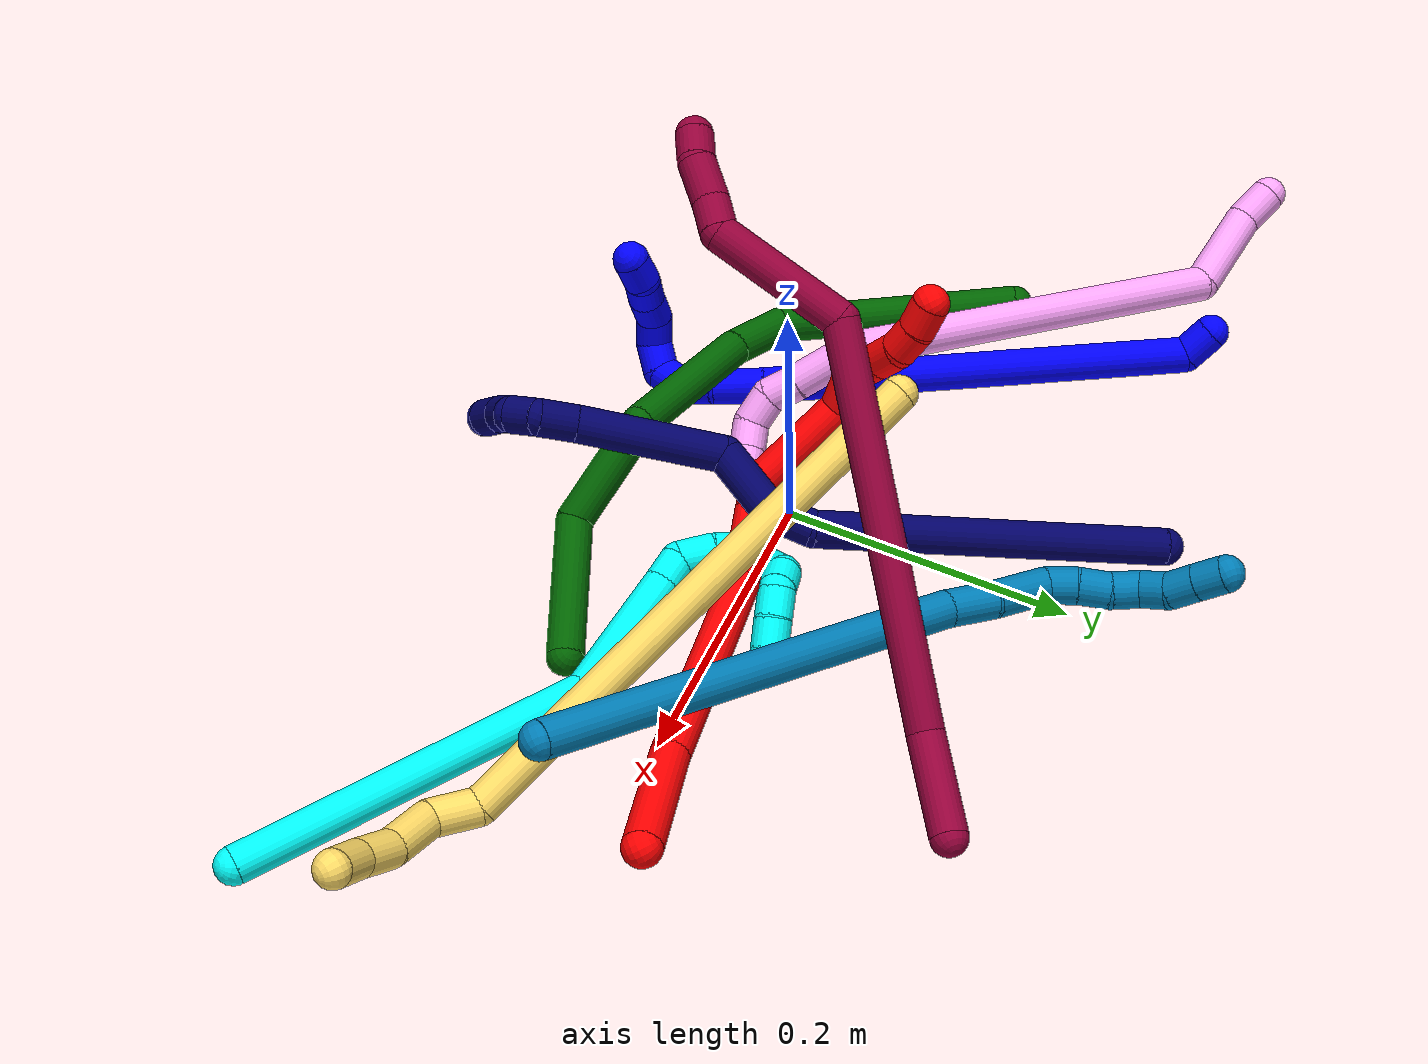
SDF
<sdf version="1.7">
 <world name="default">
  <plugin name="TubeGeneratorPlugin" filename="libtube_generator_plugin.so"/>
  <model name="photoneo_s_sensor">
   <static>1</static>
   <pose>0 0 2 1.57079 1.57079 3.14159</pose>
   <link name="link">
    <inertial><mass>0.1</mass></inertial>
    <sensor name="sensor" type="depth">
     <update_rate>30</update_rate>
     <camera>
      <horizontal_fov>1.22</horizontal_fov>
      <image><width>1920</width><height>1200</height><format>B8G8R8</format></image>
      <clip><near>0.1</near><far>4</far></clip>
      <depth_camera><output>points</output></depth_camera>
     </camera>
     <plugin name="camera_plugin" filename="libgazebo_ros_depth_camera.so">
      <baseline>0.2</baseline>
      <alwaysOn>1</alwaysOn>
      <updateRate>0.0</updateRate>
      <cameraName>camera_ir</cameraName>
      <imageTopicName>/camera/color/image_raw</imageTopicName>
      <cameraInfoTopicName>/camera/color/camera_info</cameraInfoTopicName>
      <depthImageTopicName>/camera/depth/image_raw</depthImageTopicName>
      <depthImageCameraInfoTopicName>/camera/depth/camera_info</depthImageCameraInfoTopicName>
      <pointCloudTopicName>/camera/depth/points</pointCloudTopicName>
      <frameName>fr_optical</frameName>
      <pointCloudCutoff>0.1</pointCloudCutoff>
      <pointCloudCutoffMax>2.0</pointCloudCutoffMax>
      <distortionK1>0</distortionK1>
      <distortionK2>0</distortionK2>
      <distortionK3>0</distortionK3>
      <distortionT1>0</distortionT1>
      <distortionT2>0</distortionT2>
      <CxPrime>0</CxPrime>
      <Cx>0</Cx>
      <Cy>0</Cy>
      <focalLength>0</focalLength>
      <hackBaseline>0</hackBaseline>
     </plugin>
    </sensor>
   </link>
  </model>
  <gravity>0 0 -9.8</gravity>
  <magnetic_field>6e-06 2.3e-05 -4.2e-05</magnetic_field>
  <atmosphere type="adiabatic"/>
  <physics name="default_physics" default="0" type="ode">
   <max_step_size>0.003</max_step_size>
   <real_time_factor>1</real_time_factor>
   <real_time_update_rate>1000</real_time_update_rate>
   <max_contacts>10000</max_contacts>
   <ode>
    <solver>
     <type>quick</type>
     <iters>100</iters>
     <sor>1.3</sor>
     <use_dynamic_moi_rescaling>0</use_dynamic_moi_rescaling>
    </solver>
    <constraints>
     <contact_max_correcting_vel>0</contact_max_correcting_vel>
     <contact_surface_layer>0.001</contact_surface_layer>
     <cfm>0</cfm>
     <erp>0.2</erp>
    </constraints>
   </ode>
  </physics>
  <scene><ambient>0.4 0.4 0.4 1</ambient><background>0.7 0.7 0.7 1</background><shadows>0</shadows></scene>
  <audio><device>default</device></audio>
  <spherical_coordinates>
   <surface_model>EARTH_WGS84</surface_model>
   <latitude_deg>0</latitude_deg>
   <longitude_deg>0</longitude_deg>
   <elevation>0</elevation>
   <heading_deg>0</heading_deg>
  </spherical_coordinates>
  <model name="bin">
   <static>1</static>
   <link name="bottom">
    <collision name="collision-bottom">
     <pose>0 0 -0.01 0 -0 0</pose>
     <geometry><box><size>0.8 0.6 0.02</size></box></geometry>
     <surface>
      <friction><ode><mu>100</mu><mu2>100</mu2></ode></friction>
      <contact><collide_bitmask>65535</collide_bitmask></contact>
     </surface>
    </collision>
   </link>
   <link name="west_wall">
    <collision name="collision-west_wall">
     <pose>-0.41 0 0.1 0 -0 0</pose>
     <geometry><box><size>0.02 0.6 0.2</size></box></geometry>
     <surface>
      <friction><ode><mu>100</mu><mu2>100</mu2></ode></friction>
      <contact><collide_bitmask>65535</collide_bitmask></contact>
     </surface>
    </collision>
   </link>
   <link name="east_wall">
    <collision name="collision-east_wall">
     <pose>0.41 0 0.1 0 -0 0</pose>
     <geometry><box><size>0.02 0.6 0.2</size></box></geometry>
     <surface>
      <friction><ode><mu>100</mu><mu2>100</mu2></ode></friction>
      <contact><collide_bitmask>65535</collide_bitmask></contact>
     </surface>
    </collision>
   </link>
   <link name="south_wall">
    <collision name="collision-south_wall">
     <pose>0 -0.31 0.1 0 -0 0</pose>
     <geometry><box><size>0.8 0.02 0.2</size></box></geometry>
     <surface>
      <friction><ode><mu>100</mu><mu2>100</mu2></ode></friction>
      <contact><collide_bitmask>65535</collide_bitmask></contact>
     </surface>
    </collision>
   </link>
   <link name="north_wall">
    <collision name="collision-north_wall">
     <pose>0 0.31 0.1 0 -0 0</pose>
     <geometry><box><size>0.8 0.02 0.2</size></box></geometry>
     <surface>
      <friction><ode><mu>100</mu><mu2>100</mu2></ode></friction>
      <contact><collide_bitmask>65535</collide_bitmask></contact>
     </surface>
    </collision>
   </link>
  </model>
  <model name="1">
   <static>0</static>
   <link name="1">
    <collision name="collision-cylinder-e_1_1_4">
     <pose>-0.000129 -0.011569 0.001819 1.41482 -0.011016 -0.009419</pose>
     <geometry><cylinder><radius>0.0125</radius><length>0.023423</length></cylinder></geometry>
     <surface>
      <friction><ode><mu>1.16</mu><mu2>1.16</mu2><slip1>0</slip1><slip2>0</slip2></ode></friction>
      <contact><ode><kp>1e+06</kp><kd>1</kd><max_vel>0</max_vel><min_depth>0.001</min_depth></ode></contact>
     </surface>
    </collision>
    <visual name="visual-cylinder-e_1_1_4">
     <pose>-0.000129 -0.011569 0.001819 1.41482 -0.011016 -0.009419</pose>
     <geometry><cylinder><radius>0.0125</radius><length>0.023423</length></cylinder></geometry>
     <material><ambient>0 0 1 1</ambient></material>
    </visual>
    <collision name="collision-cylinder-e_2_4_5">
     <pose>0.060893 -0.14702 -0.052724 1.99777 0.422276 0.642876</pose>
     <geometry><cylinder><radius>0.0125</radius><length>0.298415</length></cylinder></geometry>
     <surface>
      <friction><ode><mu>1.16</mu><mu2>1.16</mu2><slip1>0</slip1><slip2>0</slip2></ode></friction>
      <contact><ode><kp>1e+06</kp><kd>1</kd><max_vel>0</max_vel><min_depth>0.001</min_depth></ode></contact>
     </surface>
    </collision>
    <visual name="visual-cylinder-e_2_4_5">
     <pose>0.060893 -0.14702 -0.052724 1.99777 0.422276 0.642876</pose>
     <geometry><cylinder><radius>0.0125</radius><length>0.298415</length></cylinder></geometry>
     <material><ambient>0 0 1 1</ambient></material>
    </visual>
    <collision name="collision-cylinder-e_3_5_6">
     <pose>0.13036 -0.28511 -0.115248 1.98001 0.49282 0.731952</pose>
     <geometry><cylinder><radius>0.0125</radius><length>0.035156</length></cylinder></geometry>
     <surface>
      <friction><ode><mu>1.16</mu><mu2>1.16</mu2><slip1>0</slip1><slip2>0</slip2></ode></friction>
      <contact><ode><kp>1e+06</kp><kd>1</kd><max_vel>0</max_vel><min_depth>0.001</min_depth></ode></contact>
     </surface>
    </collision>
    <visual name="visual-cylinder-e_3_5_6">
     <pose>0.13036 -0.28511 -0.115248 1.98001 0.49282 0.731952</pose>
     <geometry><cylinder><radius>0.0125</radius><length>0.035156</length></cylinder></geometry>
     <material><ambient>0 0 1 1</ambient></material>
    </visual>
    <collision name="collision-cylinder-e_4_6_7">
     <pose>0.145175 -0.307591 -0.122555 1.7084 0.661197 0.750634</pose>
     <geometry><cylinder><radius>0.0125</radius><length>0.021166</length></cylinder></geometry>
     <surface>
      <friction><ode><mu>1.16</mu><mu2>1.16</mu2><slip1>0</slip1><slip2>0</slip2></ode></friction>
      <contact><ode><kp>1e+06</kp><kd>1</kd><max_vel>0</max_vel><min_depth>0.001</min_depth></ode></contact>
     </surface>
    </collision>
    <visual name="visual-cylinder-e_4_6_7">
     <pose>0.145175 -0.307591 -0.122555 1.7084 0.661197 0.750634</pose>
     <geometry><cylinder><radius>0.0125</radius><length>0.021166</length></cylinder></geometry>
     <material><ambient>0 0 1 1</ambient></material>
    </visual>
    <collision name="collision-cylinder-e_5_7_8">
     <pose>0.161134 -0.319378 -0.124914 1.90321 1.19645 1.52611</pose>
     <geometry><cylinder><radius>0.0125</radius><length>0.020328</length></cylinder></geometry>
     <surface>
      <friction><ode><mu>1.16</mu><mu2>1.16</mu2><slip1>0</slip1><slip2>0</slip2></ode></friction>
      <contact><ode><kp>1e+06</kp><kd>1</kd><max_vel>0</max_vel><min_depth>0.001</min_depth></ode></contact>
     </surface>
    </collision>
    <visual name="visual-cylinder-e_5_7_8">
     <pose>0.161134 -0.319378 -0.124914 1.90321 1.19645 1.52611</pose>
     <geometry><cylinder><radius>0.0125</radius><length>0.020328</length></cylinder></geometry>
     <material><ambient>0 0 1 1</ambient></material>
    </visual>
    <collision name="collision-cylinder-e_6_8_9">
     <pose>0.180108 -0.318916 -0.129129 -2.21772 1.08843 -1.76476</pose>
     <geometry><cylinder><radius>0.0125</radius><length>0.021479</length></cylinder></geometry>
     <surface>
      <friction><ode><mu>1.16</mu><mu2>1.16</mu2><slip1>0</slip1><slip2>0</slip2></ode></friction>
      <contact><ode><kp>1e+06</kp><kd>1</kd><max_vel>0</max_vel><min_depth>0.001</min_depth></ode></contact>
     </surface>
    </collision>
    <visual name="visual-cylinder-e_6_8_9">
     <pose>0.180108 -0.318916 -0.129129 -2.21772 1.08843 -1.76476</pose>
     <geometry><cylinder><radius>0.0125</radius><length>0.021479</length></cylinder></geometry>
     <material><ambient>0 0 1 1</ambient></material>
    </visual>
    <collision name="collision-cylinder-e_7_9_10">
     <pose>0.193299 -0.309052 -0.139332 -2.45613 0.376378 -0.980528</pose>
     <geometry><cylinder><radius>0.0125</radius><length>0.020004</length></cylinder></geometry>
     <surface>
      <friction><ode><mu>1.16</mu><mu2>1.16</mu2><slip1>0</slip1><slip2>0</slip2></ode></friction>
      <contact><ode><kp>1e+06</kp><kd>1</kd><max_vel>0</max_vel><min_depth>0.001</min_depth></ode></contact>
     </surface>
    </collision>
    <visual name="visual-cylinder-e_7_9_10">
     <pose>0.193299 -0.309052 -0.139332 -2.45613 0.376378 -0.980528</pose>
     <geometry><cylinder><radius>0.0125</radius><length>0.020004</length></cylinder></geometry>
     <material><ambient>0 0 1 1</ambient></material>
    </visual>
    <collision name="collision-cylinder-e_8_10_11">
     <pose>0.199154 -0.300576 -0.155949 -2.87331 0.219604 -1.36994</pose>
     <geometry><cylinder><radius>0.0125</radius><length>0.020011</length></cylinder></geometry>
     <surface>
      <friction><ode><mu>1.16</mu><mu2>1.16</mu2><slip1>0</slip1><slip2>0</slip2></ode></friction>
      <contact><ode><kp>1e+06</kp><kd>1</kd><max_vel>0</max_vel><min_depth>0.001</min_depth></ode></contact>
     </surface>
    </collision>
    <visual name="visual-cylinder-e_8_10_11">
     <pose>0.199154 -0.300576 -0.155949 -2.87331 0.219604 -1.36994</pose>
     <geometry><cylinder><radius>0.0125</radius><length>0.020011</length></cylinder></geometry>
     <material><ambient>0 0 1 1</ambient></material>
    </visual>
    <collision name="collision-cylinder-e_9_11_12">
     <pose>0.201592 -0.294851 -0.17486 -2.82259 0.025782 -0.159933</pose>
     <geometry><cylinder><radius>0.0125</radius><length>0.020006</length></cylinder></geometry>
     <surface>
      <friction><ode><mu>1.16</mu><mu2>1.16</mu2><slip1>0</slip1><slip2>0</slip2></ode></friction>
      <contact><ode><kp>1e+06</kp><kd>1</kd><max_vel>0</max_vel><min_depth>0.001</min_depth></ode></contact>
     </surface>
    </collision>
    <visual name="visual-cylinder-e_9_11_12">
     <pose>0.201592 -0.294851 -0.17486 -2.82259 0.025782 -0.159933</pose>
     <geometry><cylinder><radius>0.0125</radius><length>0.020006</length></cylinder></geometry>
     <material><ambient>0 0 1 1</ambient></material>
    </visual>
    <collision name="collision-cylinder-e_10_12_2">
     <pose>0.205515 -0.289786 -0.193463 -2.93287 0.375018 -2.1328</pose>
     <geometry><cylinder><radius>0.0125</radius><length>0.020012</length></cylinder></geometry>
     <surface>
      <friction><ode><mu>1.16</mu><mu2>1.16</mu2><slip1>0</slip1><slip2>0</slip2></ode></friction>
      <contact><ode><kp>1e+06</kp><kd>1</kd><max_vel>0</max_vel><min_depth>0.001</min_depth></ode></contact>
     </surface>
    </collision>
    <visual name="visual-cylinder-e_10_12_2">
     <pose>0.205515 -0.289786 -0.193463 -2.93287 0.375018 -2.1328</pose>
     <geometry><cylinder><radius>0.0125</radius><length>0.020012</length></cylinder></geometry>
     <material><ambient>0 0 1 1</ambient></material>
    </visual>
    <collision name="collision-sphere-2">
     <pose>0.20918 -0.287856 -0.202572 0 -0 0</pose>
     <geometry><sphere><radius>0.0125</radius></sphere></geometry>
     <surface>
      <friction><ode><mu>1.16</mu><mu2>1.16</mu2><slip1>0</slip1><slip2>0</slip2></ode></friction>
      <contact><ode><kp>1e+06</kp><kd>1</kd><max_vel>0</max_vel><min_depth>0.001</min_depth></ode></contact>
     </surface>
    </collision>
    <visual name="visual-sphere-2">
     <pose>0.20918 -0.287856 -0.202572 0 -0 0</pose>
     <geometry><sphere><radius>0.0125</radius></sphere></geometry>
     <material><ambient>0 0 1 1</ambient></material>
    </visual>
    <collision name="collision-sphere-12">
     <pose>0.20185 -0.291715 -0.184355 0 -0 0</pose>
     <geometry><sphere><radius>0.0125</radius></sphere></geometry>
     <surface>
      <friction><ode><mu>1.16</mu><mu2>1.16</mu2><slip1>0</slip1><slip2>0</slip2></ode></friction>
      <contact><ode><kp>1e+06</kp><kd>1</kd><max_vel>0</max_vel><min_depth>0.001</min_depth></ode></contact>
     </surface>
    </collision>
    <visual name="visual-sphere-12">
     <pose>0.20185 -0.291715 -0.184355 0 -0 0</pose>
     <geometry><sphere><radius>0.0125</radius></sphere></geometry>
     <material><ambient>0 0 1 1</ambient></material>
    </visual>
    <collision name="collision-sphere-11">
     <pose>0.201334 -0.297987 -0.165365 0 -0 0</pose>
     <geometry><sphere><radius>0.0125</radius></sphere></geometry>
     <surface>
      <friction><ode><mu>1.16</mu><mu2>1.16</mu2><slip1>0</slip1><slip2>0</slip2></ode></friction>
      <contact><ode><kp>1e+06</kp><kd>1</kd><max_vel>0</max_vel><min_depth>0.001</min_depth></ode></contact>
     </surface>
    </collision>
    <visual name="visual-sphere-11">
     <pose>0.201334 -0.297987 -0.165365 0 -0 0</pose>
     <geometry><sphere><radius>0.0125</radius></sphere></geometry>
     <material><ambient>0 0 1 1</ambient></material>
    </visual>
    <collision name="collision-sphere-10">
     <pose>0.196975 -0.303164 -0.146533 0 -0 0</pose>
     <geometry><sphere><radius>0.0125</radius></sphere></geometry>
     <surface>
      <friction><ode><mu>1.16</mu><mu2>1.16</mu2><slip1>0</slip1><slip2>0</slip2></ode></friction>
      <contact><ode><kp>1e+06</kp><kd>1</kd><max_vel>0</max_vel><min_depth>0.001</min_depth></ode></contact>
     </surface>
    </collision>
    <visual name="visual-sphere-10">
     <pose>0.196975 -0.303164 -0.146533 0 -0 0</pose>
     <geometry><sphere><radius>0.0125</radius></sphere></geometry>
     <material><ambient>0 0 1 1</ambient></material>
    </visual>
    <collision name="collision-sphere-9">
     <pose>0.189622 -0.314941 -0.132132 0 -0 0</pose>
     <geometry><sphere><radius>0.0125</radius></sphere></geometry>
     <surface>
      <friction><ode><mu>1.16</mu><mu2>1.16</mu2><slip1>0</slip1><slip2>0</slip2></ode></friction>
      <contact><ode><kp>1e+06</kp><kd>1</kd><max_vel>0</max_vel><min_depth>0.001</min_depth></ode></contact>
     </surface>
    </collision>
    <visual name="visual-sphere-9">
     <pose>0.189622 -0.314941 -0.132132 0 -0 0</pose>
     <geometry><sphere><radius>0.0125</radius></sphere></geometry>
     <material><ambient>0 0 1 1</ambient></material>
    </visual>
    <collision name="collision-sphere-4">
     <pose>-0.000258 -0.023137 0.003639 0 -0 0</pose>
     <geometry><sphere><radius>0.0125</radius></sphere></geometry>
     <surface>
      <friction><ode><mu>1.16</mu><mu2>1.16</mu2><slip1>0</slip1><slip2>0</slip2></ode></friction>
      <contact><ode><kp>1e+06</kp><kd>1</kd><max_vel>0</max_vel><min_depth>0.001</min_depth></ode></contact>
     </surface>
    </collision>
    <visual name="visual-sphere-4">
     <pose>-0.000258 -0.023137 0.003639 0 -0 0</pose>
     <geometry><sphere><radius>0.0125</radius></sphere></geometry>
     <material><ambient>0 0 1 1</ambient></material>
    </visual>
    <collision name="collision-sphere-1">
     <geometry><sphere><radius>0.0125</radius></sphere></geometry>
     <surface>
      <friction><ode><mu>1.16</mu><mu2>1.16</mu2><slip1>0</slip1><slip2>0</slip2></ode></friction>
      <contact><ode><kp>1e+06</kp><kd>1</kd><max_vel>0</max_vel><min_depth>0.001</min_depth></ode></contact>
     </surface>
    </collision>
    <visual name="visual-sphere-1">
     <geometry><sphere><radius>0.0125</radius></sphere></geometry>
     <material><ambient>0 0 1 1</ambient></material>
    </visual>
    <collision name="collision-sphere-8">
     <pose>0.170594 -0.322891 -0.126126 0 -0 0</pose>
     <geometry><sphere><radius>0.0125</radius></sphere></geometry>
     <surface>
      <friction><ode><mu>1.16</mu><mu2>1.16</mu2><slip1>0</slip1><slip2>0</slip2></ode></friction>
      <contact><ode><kp>1e+06</kp><kd>1</kd><max_vel>0</max_vel><min_depth>0.001</min_depth></ode></contact>
     </surface>
    </collision>
    <visual name="visual-sphere-8">
     <pose>0.170594 -0.322891 -0.126126 0 -0 0</pose>
     <geometry><sphere><radius>0.0125</radius></sphere></geometry>
     <material><ambient>0 0 1 1</ambient></material>
    </visual>
    <collision name="collision-sphere-5">
     <pose>0.122044 -0.270902 -0.109086 0 -0 0</pose>
     <geometry><sphere><radius>0.0125</radius></sphere></geometry>
     <surface>
      <friction><ode><mu>1.16</mu><mu2>1.16</mu2><slip1>0</slip1><slip2>0</slip2></ode></friction>
      <contact><ode><kp>1e+06</kp><kd>1</kd><max_vel>0</max_vel><min_depth>0.001</min_depth></ode></contact>
     </surface>
    </collision>
    <visual name="visual-sphere-5">
     <pose>0.122044 -0.270902 -0.109086 0 -0 0</pose>
     <geometry><sphere><radius>0.0125</radius></sphere></geometry>
     <material><ambient>0 0 1 1</ambient></material>
    </visual>
    <collision name="collision-sphere-6">
     <pose>0.138677 -0.299317 -0.121409 0 -0 0</pose>
     <geometry><sphere><radius>0.0125</radius></sphere></geometry>
     <surface>
      <friction><ode><mu>1.16</mu><mu2>1.16</mu2><slip1>0</slip1><slip2>0</slip2></ode></friction>
      <contact><ode><kp>1e+06</kp><kd>1</kd><max_vel>0</max_vel><min_depth>0.001</min_depth></ode></contact>
     </surface>
    </collision>
    <visual name="visual-sphere-6">
     <pose>0.138677 -0.299317 -0.121409 0 -0 0</pose>
     <geometry><sphere><radius>0.0125</radius></sphere></geometry>
     <material><ambient>0 0 1 1</ambient></material>
    </visual>
    <collision name="collision-sphere-7">
     <pose>0.151674 -0.315865 -0.123701 0 -0 0</pose>
     <geometry><sphere><radius>0.0125</radius></sphere></geometry>
     <surface>
      <friction><ode><mu>1.16</mu><mu2>1.16</mu2><slip1>0</slip1><slip2>0</slip2></ode></friction>
      <contact><ode><kp>1e+06</kp><kd>1</kd><max_vel>0</max_vel><min_depth>0.001</min_depth></ode></contact>
     </surface>
    </collision>
    <visual name="visual-sphere-7">
     <pose>0.151674 -0.315865 -0.123701 0 -0 0</pose>
     <geometry><sphere><radius>0.0125</radius></sphere></geometry>
     <material><ambient>0 0 1 1</ambient></material>
    </visual>
    <inertial>
     <pose>0.097932 -0.19583 -0.081854 0 -0 0</pose>
     <mass>0.5</mass>
     <inertia>
      <ixx>0.002866</ixx>
      <ixy>0</ixy>
      <ixz>0</ixz>
      <iyy>0.000957</iyy>
      <iyz>0</iyz>
      <izz>0.000918</izz>
     </inertia>
    </inertial>
   </link>
   <pose>-0.248468 0.211805 0.024817 2.69146 -0.083425 -2.18895</pose>
  </model>
  <model name="2">
   <static>0</static>
   <link name="2">
    <collision name="collision-cylinder-e_1_1_4">
     <pose>-0.0279 -0.027557 -0.011878 1.97777 -0.749013 -1.07707</pose>
     <geometry><cylinder><radius>0.0125</radius><length>0.081947</length></cylinder></geometry>
     <surface>
      <friction><ode><mu>1.16</mu><mu2>1.16</mu2><slip1>0</slip1><slip2>0</slip2></ode></friction>
      <contact><ode><kp>1e+06</kp><kd>1</kd><max_vel>0</max_vel><min_depth>0.001</min_depth></ode></contact>
     </surface>
    </collision>
    <visual name="visual-cylinder-e_1_1_4">
     <pose>-0.0279 -0.027557 -0.011878 1.97777 -0.749013 -1.07707</pose>
     <geometry><cylinder><radius>0.0125</radius><length>0.081947</length></cylinder></geometry>
     <material><ambient>1 0 0 1</ambient></material>
    </visual>
    <collision name="collision-cylinder-e_2_4_5">
     <pose>-0.110259 -0.104633 -0.056803 2.15926 -0.740907 -1.25607</pose>
     <geometry><cylinder><radius>0.0125</radius><length>0.161372</length></cylinder></geometry>
     <surface>
      <friction><ode><mu>1.16</mu><mu2>1.16</mu2><slip1>0</slip1><slip2>0</slip2></ode></friction>
      <contact><ode><kp>1e+06</kp><kd>1</kd><max_vel>0</max_vel><min_depth>0.001</min_depth></ode></contact>
     </surface>
    </collision>
    <visual name="visual-cylinder-e_2_4_5">
     <pose>-0.110259 -0.104633 -0.056803 2.15926 -0.740907 -1.25607</pose>
     <geometry><cylinder><radius>0.0125</radius><length>0.161372</length></cylinder></geometry>
     <material><ambient>1 0 0 1</ambient></material>
    </visual>
    <collision name="collision-cylinder-e_3_5_6">
     <pose>-0.188735 -0.165083 -0.101712 2.39711 -0.979389 -1.87712</pose>
     <geometry><cylinder><radius>0.0125</radius><length>0.05786</length></cylinder></geometry>
     <surface>
      <friction><ode><mu>1.16</mu><mu2>1.16</mu2><slip1>0</slip1><slip2>0</slip2></ode></friction>
      <contact><ode><kp>1e+06</kp><kd>1</kd><max_vel>0</max_vel><min_depth>0.001</min_depth></ode></contact>
     </surface>
    </collision>
    <visual name="visual-cylinder-e_3_5_6">
     <pose>-0.188735 -0.165083 -0.101712 2.39711 -0.979389 -1.87712</pose>
     <geometry><cylinder><radius>0.0125</radius><length>0.05786</length></cylinder></geometry>
     <material><ambient>1 0 0 1</ambient></material>
    </visual>
    <collision name="collision-cylinder-e_4_6_7">
     <pose>-0.220841 -0.174942 -0.120636 -2.99122 -0.847495 2.81065</pose>
     <geometry><cylinder><radius>0.0125</radius><length>0.021584</length></cylinder></geometry>
     <surface>
      <friction><ode><mu>1.16</mu><mu2>1.16</mu2><slip1>0</slip1><slip2>0</slip2></ode></friction>
      <contact><ode><kp>1e+06</kp><kd>1</kd><max_vel>0</max_vel><min_depth>0.001</min_depth></ode></contact>
     </surface>
    </collision>
    <visual name="visual-cylinder-e_4_6_7">
     <pose>-0.220841 -0.174942 -0.120636 -2.99122 -0.847495 2.81065</pose>
     <geometry><cylinder><radius>0.0125</radius><length>0.021584</length></cylinder></geometry>
     <material><ambient>1 0 0 1</ambient></material>
    </visual>
    <collision name="collision-cylinder-e_5_7_8">
     <pose>-0.238582 -0.170751 -0.160245 -3.04599 -0.287039 2.50224</pose>
     <geometry><cylinder><radius>0.0125</radius><length>0.068181</length></cylinder></geometry>
     <surface>
      <friction><ode><mu>1.16</mu><mu2>1.16</mu2><slip1>0</slip1><slip2>0</slip2></ode></friction>
      <contact><ode><kp>1e+06</kp><kd>1</kd><max_vel>0</max_vel><min_depth>0.001</min_depth></ode></contact>
     </surface>
    </collision>
    <visual name="visual-cylinder-e_5_7_8">
     <pose>-0.238582 -0.170751 -0.160245 -3.04599 -0.287039 2.50224</pose>
     <geometry><cylinder><radius>0.0125</radius><length>0.068181</length></cylinder></geometry>
     <material><ambient>1 0 0 1</ambient></material>
    </visual>
    <collision name="collision-cylinder-e_6_8_9">
     <pose>-0.25401 -0.159086 -0.202769 -2.43347 -0.414231 1.03383</pose>
     <geometry><cylinder><radius>0.0125</radius><length>0.0287</length></cylinder></geometry>
     <surface>
      <friction><ode><mu>1.16</mu><mu2>1.16</mu2><slip1>0</slip1><slip2>0</slip2></ode></friction>
      <contact><ode><kp>1e+06</kp><kd>1</kd><max_vel>0</max_vel><min_depth>0.001</min_depth></ode></contact>
     </surface>
    </collision>
    <visual name="visual-cylinder-e_6_8_9">
     <pose>-0.25401 -0.159086 -0.202769 -2.43347 -0.414231 1.03383</pose>
     <geometry><cylinder><radius>0.0125</radius><length>0.0287</length></cylinder></geometry>
     <material><ambient>1 0 0 1</ambient></material>
    </visual>
    <collision name="collision-cylinder-e_7_9_10">
     <pose>-0.258062 -0.146257 -0.221696 -2.69502 0.172028 -0.725832</pose>
     <geometry><cylinder><radius>0.0125</radius><length>0.020139</length></cylinder></geometry>
     <surface>
      <friction><ode><mu>1.16</mu><mu2>1.16</mu2><slip1>0</slip1><slip2>0</slip2></ode></friction>
      <contact><ode><kp>1e+06</kp><kd>1</kd><max_vel>0</max_vel><min_depth>0.001</min_depth></ode></contact>
     </surface>
    </collision>
    <visual name="visual-cylinder-e_7_9_10">
     <pose>-0.258062 -0.146257 -0.221696 -2.69502 0.172028 -0.725832</pose>
     <geometry><cylinder><radius>0.0125</radius><length>0.020139</length></cylinder></geometry>
     <material><ambient>1 0 0 1</ambient></material>
    </visual>
    <collision name="collision-cylinder-e_8_10_11">
     <pose>-0.25434 -0.135648 -0.238215 -2.44566 0.199815 -0.539251</pose>
     <geometry><cylinder><radius>0.0125</radius><length>0.020132</length></cylinder></geometry>
     <surface>
      <friction><ode><mu>1.16</mu><mu2>1.16</mu2><slip1>0</slip1><slip2>0</slip2></ode></friction>
      <contact><ode><kp>1e+06</kp><kd>1</kd><max_vel>0</max_vel><min_depth>0.001</min_depth></ode></contact>
     </surface>
    </collision>
    <visual name="visual-cylinder-e_8_10_11">
     <pose>-0.25434 -0.135648 -0.238215 -2.44566 0.199815 -0.539251</pose>
     <geometry><cylinder><radius>0.0125</radius><length>0.020132</length></cylinder></geometry>
     <material><ambient>1 0 0 1</ambient></material>
    </visual>
    <collision name="collision-cylinder-e_9_11_12">
     <pose>-0.253776 -0.12375 -0.253992 -2.54497 -0.143542 0.459375</pose>
     <geometry><cylinder><radius>0.0125</radius><length>0.020045</length></cylinder></geometry>
     <surface>
      <friction><ode><mu>1.16</mu><mu2>1.16</mu2><slip1>0</slip1><slip2>0</slip2></ode></friction>
      <contact><ode><kp>1e+06</kp><kd>1</kd><max_vel>0</max_vel><min_depth>0.001</min_depth></ode></contact>
     </surface>
    </collision>
    <visual name="visual-cylinder-e_9_11_12">
     <pose>-0.253776 -0.12375 -0.253992 -2.54497 -0.143542 0.459375</pose>
     <geometry><cylinder><radius>0.0125</radius><length>0.020045</length></cylinder></geometry>
     <material><ambient>1 0 0 1</ambient></material>
    </visual>
    <collision name="collision-cylinder-e_10_12_2">
     <pose>-0.258653 -0.112425 -0.269645 -2.48398 -0.350828 0.958193</pose>
     <geometry><cylinder><radius>0.0125</radius><length>0.020041</length></cylinder></geometry>
     <surface>
      <friction><ode><mu>1.16</mu><mu2>1.16</mu2><slip1>0</slip1><slip2>0</slip2></ode></friction>
      <contact><ode><kp>1e+06</kp><kd>1</kd><max_vel>0</max_vel><min_depth>0.001</min_depth></ode></contact>
     </surface>
    </collision>
    <visual name="visual-cylinder-e_10_12_2">
     <pose>-0.258653 -0.112425 -0.269645 -2.48398 -0.350828 0.958193</pose>
     <geometry><cylinder><radius>0.0125</radius><length>0.020041</length></cylinder></geometry>
     <material><ambient>1 0 0 1</ambient></material>
    </visual>
    <collision name="collision-sphere-2">
     <pose>-0.262097 -0.106673 -0.277093 0 -0 0</pose>
     <geometry><sphere><radius>0.0125</radius></sphere></geometry>
     <surface>
      <friction><ode><mu>1.16</mu><mu2>1.16</mu2><slip1>0</slip1><slip2>0</slip2></ode></friction>
      <contact><ode><kp>1e+06</kp><kd>1</kd><max_vel>0</max_vel><min_depth>0.001</min_depth></ode></contact>
     </surface>
    </collision>
    <visual name="visual-sphere-2">
     <pose>-0.262097 -0.106673 -0.277093 0 -0 0</pose>
     <geometry><sphere><radius>0.0125</radius></sphere></geometry>
     <material><ambient>1 0 0 1</ambient></material>
    </visual>
    <collision name="collision-sphere-12">
     <pose>-0.25521 -0.118177 -0.262197 0 -0 0</pose>
     <geometry><sphere><radius>0.0125</radius></sphere></geometry>
     <surface>
      <friction><ode><mu>1.16</mu><mu2>1.16</mu2><slip1>0</slip1><slip2>0</slip2></ode></friction>
      <contact><ode><kp>1e+06</kp><kd>1</kd><max_vel>0</max_vel><min_depth>0.001</min_depth></ode></contact>
     </surface>
    </collision>
    <visual name="visual-sphere-12">
     <pose>-0.25521 -0.118177 -0.262197 0 -0 0</pose>
     <geometry><sphere><radius>0.0125</radius></sphere></geometry>
     <material><ambient>1 0 0 1</ambient></material>
    </visual>
    <collision name="collision-sphere-11">
     <pose>-0.252342 -0.129323 -0.245786 0 -0 0</pose>
     <geometry><sphere><radius>0.0125</radius></sphere></geometry>
     <surface>
      <friction><ode><mu>1.16</mu><mu2>1.16</mu2><slip1>0</slip1><slip2>0</slip2></ode></friction>
      <contact><ode><kp>1e+06</kp><kd>1</kd><max_vel>0</max_vel><min_depth>0.001</min_depth></ode></contact>
     </surface>
    </collision>
    <visual name="visual-sphere-11">
     <pose>-0.252342 -0.129323 -0.245786 0 -0 0</pose>
     <geometry><sphere><radius>0.0125</radius></sphere></geometry>
     <material><ambient>1 0 0 1</ambient></material>
    </visual>
    <collision name="collision-sphere-10">
     <pose>-0.256338 -0.141973 -0.230643 0 -0 0</pose>
     <geometry><sphere><radius>0.0125</radius></sphere></geometry>
     <surface>
      <friction><ode><mu>1.16</mu><mu2>1.16</mu2><slip1>0</slip1><slip2>0</slip2></ode></friction>
      <contact><ode><kp>1e+06</kp><kd>1</kd><max_vel>0</max_vel><min_depth>0.001</min_depth></ode></contact>
     </surface>
    </collision>
    <visual name="visual-sphere-10">
     <pose>-0.256338 -0.141973 -0.230643 0 -0 0</pose>
     <geometry><sphere><radius>0.0125</radius></sphere></geometry>
     <material><ambient>1 0 0 1</ambient></material>
    </visual>
    <collision name="collision-sphere-9">
     <pose>-0.259785 -0.150542 -0.212748 0 -0 0</pose>
     <geometry><sphere><radius>0.0125</radius></sphere></geometry>
     <surface>
      <friction><ode><mu>1.16</mu><mu2>1.16</mu2><slip1>0</slip1><slip2>0</slip2></ode></friction>
      <contact><ode><kp>1e+06</kp><kd>1</kd><max_vel>0</max_vel><min_depth>0.001</min_depth></ode></contact>
     </surface>
    </collision>
    <visual name="visual-sphere-9">
     <pose>-0.259785 -0.150542 -0.212748 0 -0 0</pose>
     <geometry><sphere><radius>0.0125</radius></sphere></geometry>
     <material><ambient>1 0 0 1</ambient></material>
    </visual>
    <collision name="collision-sphere-4">
     <pose>-0.055799 -0.055113 -0.023756 0 -0 0</pose>
     <geometry><sphere><radius>0.0125</radius></sphere></geometry>
     <surface>
      <friction><ode><mu>1.16</mu><mu2>1.16</mu2><slip1>0</slip1><slip2>0</slip2></ode></friction>
      <contact><ode><kp>1e+06</kp><kd>1</kd><max_vel>0</max_vel><min_depth>0.001</min_depth></ode></contact>
     </surface>
    </collision>
    <visual name="visual-sphere-4">
     <pose>-0.055799 -0.055113 -0.023756 0 -0 0</pose>
     <geometry><sphere><radius>0.0125</radius></sphere></geometry>
     <material><ambient>1 0 0 1</ambient></material>
    </visual>
    <collision name="collision-sphere-1">
     <geometry><sphere><radius>0.0125</radius></sphere></geometry>
     <surface>
      <friction><ode><mu>1.16</mu><mu2>1.16</mu2><slip1>0</slip1><slip2>0</slip2></ode></friction>
      <contact><ode><kp>1e+06</kp><kd>1</kd><max_vel>0</max_vel><min_depth>0.001</min_depth></ode></contact>
     </surface>
    </collision>
    <visual name="visual-sphere-1">
     <geometry><sphere><radius>0.0125</radius></sphere></geometry>
     <material><ambient>1 0 0 1</ambient></material>
    </visual>
    <collision name="collision-sphere-8">
     <pose>-0.248234 -0.16763 -0.192791 0 -0 0</pose>
     <geometry><sphere><radius>0.0125</radius></sphere></geometry>
     <surface>
      <friction><ode><mu>1.16</mu><mu2>1.16</mu2><slip1>0</slip1><slip2>0</slip2></ode></friction>
      <contact><ode><kp>1e+06</kp><kd>1</kd><max_vel>0</max_vel><min_depth>0.001</min_depth></ode></contact>
     </surface>
    </collision>
    <visual name="visual-sphere-8">
     <pose>-0.248234 -0.16763 -0.192791 0 -0 0</pose>
     <geometry><sphere><radius>0.0125</radius></sphere></geometry>
     <material><ambient>1 0 0 1</ambient></material>
    </visual>
    <collision name="collision-sphere-5">
     <pose>-0.164718 -0.154154 -0.08985 0 -0 0</pose>
     <geometry><sphere><radius>0.0125</radius></sphere></geometry>
     <surface>
      <friction><ode><mu>1.16</mu><mu2>1.16</mu2><slip1>0</slip1><slip2>0</slip2></ode></friction>
      <contact><ode><kp>1e+06</kp><kd>1</kd><max_vel>0</max_vel><min_depth>0.001</min_depth></ode></contact>
     </surface>
    </collision>
    <visual name="visual-sphere-5">
     <pose>-0.164718 -0.154154 -0.08985 0 -0 0</pose>
     <geometry><sphere><radius>0.0125</radius></sphere></geometry>
     <material><ambient>1 0 0 1</ambient></material>
    </visual>
    <collision name="collision-sphere-6">
     <pose>-0.212751 -0.176012 -0.113574 0 -0 0</pose>
     <geometry><sphere><radius>0.0125</radius></sphere></geometry>
     <surface>
      <friction><ode><mu>1.16</mu><mu2>1.16</mu2><slip1>0</slip1><slip2>0</slip2></ode></friction>
      <contact><ode><kp>1e+06</kp><kd>1</kd><max_vel>0</max_vel><min_depth>0.001</min_depth></ode></contact>
     </surface>
    </collision>
    <visual name="visual-sphere-6">
     <pose>-0.212751 -0.176012 -0.113574 0 -0 0</pose>
     <geometry><sphere><radius>0.0125</radius></sphere></geometry>
     <material><ambient>1 0 0 1</ambient></material>
    </visual>
    <collision name="collision-sphere-7">
     <pose>-0.228931 -0.173872 -0.127698 0 -0 0</pose>
     <geometry><sphere><radius>0.0125</radius></sphere></geometry>
     <surface>
      <friction><ode><mu>1.16</mu><mu2>1.16</mu2><slip1>0</slip1><slip2>0</slip2></ode></friction>
      <contact><ode><kp>1e+06</kp><kd>1</kd><max_vel>0</max_vel><min_depth>0.001</min_depth></ode></contact>
     </surface>
    </collision>
    <visual name="visual-sphere-7">
     <pose>-0.228931 -0.173872 -0.127698 0 -0 0</pose>
     <geometry><sphere><radius>0.0125</radius></sphere></geometry>
     <material><ambient>1 0 0 1</ambient></material>
    </visual>
    <inertial>
     <pose>-0.159821 -0.118177 -0.110258 0 -0 0</pose>
     <mass>0.5</mass>
     <inertia>
      <ixx>-0.000215</ixx>
      <ixy>0</ixy>
      <ixz>0</ixz>
      <iyy>-9.8e-05</iyy>
      <iyz>0</iyz>
      <izz>0.000529</izz>
     </inertia>
    </inertial>
   </link>
   <pose>0.315631 0.052836 0.102913 1.92021 0.263843 0.833258</pose>
  </model>
  <model name="3">
   <static>0</static>
   <link name="3">
    <collision name="collision-cylinder-e_1_1_4">
     <pose>-0.059333 0.039546 -0.096728 -2.75349 -0.516394 1.8621</pose>
     <geometry><cylinder><radius>0.0125</radius><length>0.240338</length></cylinder></geometry>
     <surface>
      <friction><ode><mu>1.16</mu><mu2>1.16</mu2><slip1>0</slip1><slip2>0</slip2></ode></friction>
      <contact><ode><kp>1e+06</kp><kd>1</kd><max_vel>0</max_vel><min_depth>0.001</min_depth></ode></contact>
     </surface>
    </collision>
    <visual name="visual-cylinder-e_1_1_4">
     <pose>-0.059333 0.039546 -0.096728 -2.75349 -0.516394 1.8621</pose>
     <geometry><cylinder><radius>0.0125</radius><length>0.240338</length></cylinder></geometry>
     <material><ambient>0.003922 1 0.996078 1</ambient></material>
    </visual>
    <collision name="collision-cylinder-e_2_4_5">
     <pose>-0.154098 0.076052 -0.224626 3.04438 -0.846941 -2.92659</pose>
     <geometry><cylinder><radius>0.0125</radius><length>0.094578</length></cylinder></geometry>
     <surface>
      <friction><ode><mu>1.16</mu><mu2>1.16</mu2><slip1>0</slip1><slip2>0</slip2></ode></friction>
      <contact><ode><kp>1e+06</kp><kd>1</kd><max_vel>0</max_vel><min_depth>0.001</min_depth></ode></contact>
     </surface>
    </collision>
    <visual name="visual-cylinder-e_2_4_5">
     <pose>-0.154098 0.076052 -0.224626 3.04438 -0.846941 -2.92659</pose>
     <geometry><cylinder><radius>0.0125</radius><length>0.094578</length></cylinder></geometry>
     <material><ambient>0.003922 1 0.996078 1</ambient></material>
    </visual>
    <collision name="collision-cylinder-e_3_5_6">
     <pose>-0.197849 0.073395 -0.26177 -3.07773 -0.947132 3.01708</pose>
     <geometry><cylinder><radius>0.0125</radius><length>0.020499</length></cylinder></geometry>
     <surface>
      <friction><ode><mu>1.16</mu><mu2>1.16</mu2><slip1>0</slip1><slip2>0</slip2></ode></friction>
      <contact><ode><kp>1e+06</kp><kd>1</kd><max_vel>0</max_vel><min_depth>0.001</min_depth></ode></contact>
     </surface>
    </collision>
    <visual name="visual-cylinder-e_3_5_6">
     <pose>-0.197849 0.073395 -0.26177 -3.07773 -0.947132 3.01708</pose>
     <geometry><cylinder><radius>0.0125</radius><length>0.020499</length></cylinder></geometry>
     <material><ambient>0.003922 1 0.996078 1</ambient></material>
    </visual>
    <collision name="collision-cylinder-e_4_6_7">
     <pose>-0.210015 0.07979 -0.277556 -2.59176 -0.322499 1.04621</pose>
     <geometry><cylinder><radius>0.0125</radius><length>0.024268</length></cylinder></geometry>
     <surface>
      <friction><ode><mu>1.16</mu><mu2>1.16</mu2><slip1>0</slip1><slip2>0</slip2></ode></friction>
      <contact><ode><kp>1e+06</kp><kd>1</kd><max_vel>0</max_vel><min_depth>0.001</min_depth></ode></contact>
     </surface>
    </collision>
    <visual name="visual-cylinder-e_4_6_7">
     <pose>-0.210015 0.07979 -0.277556 -2.59176 -0.322499 1.04621</pose>
     <geometry><cylinder><radius>0.0125</radius><length>0.024268</length></cylinder></geometry>
     <material><ambient>0.003922 1 0.996078 1</ambient></material>
    </visual>
    <collision name="collision-cylinder-e_5_7_8">
     <pose>-0.214647 0.091779 -0.295388 -2.50121 -0.078482 0.235697</pose>
     <geometry><cylinder><radius>0.0125</radius><length>0.020064</length></cylinder></geometry>
     <surface>
      <friction><ode><mu>1.16</mu><mu2>1.16</mu2><slip1>0</slip1><slip2>0</slip2></ode></friction>
      <contact><ode><kp>1e+06</kp><kd>1</kd><max_vel>0</max_vel><min_depth>0.001</min_depth></ode></contact>
     </surface>
    </collision>
    <visual name="visual-cylinder-e_5_7_8">
     <pose>-0.214647 0.091779 -0.295388 -2.50121 -0.078482 0.235697</pose>
     <geometry><cylinder><radius>0.0125</radius><length>0.020064</length></cylinder></geometry>
     <material><ambient>0.003922 1 0.996078 1</ambient></material>
    </visual>
    <collision name="collision-cylinder-e_6_8_9">
     <pose>-0.211374 0.106343 -0.306845 -1.95152 0.413553 -0.601061</pose>
     <geometry><cylinder><radius>0.0125</radius><length>0.020205</length></cylinder></geometry>
     <surface>
      <friction><ode><mu>1.16</mu><mu2>1.16</mu2><slip1>0</slip1><slip2>0</slip2></ode></friction>
      <contact><ode><kp>1e+06</kp><kd>1</kd><max_vel>0</max_vel><min_depth>0.001</min_depth></ode></contact>
     </surface>
    </collision>
    <visual name="visual-cylinder-e_6_8_9">
     <pose>-0.211374 0.106343 -0.306845 -1.95152 0.413553 -0.601061</pose>
     <geometry><cylinder><radius>0.0125</radius><length>0.020205</length></cylinder></geometry>
     <material><ambient>0.003922 1 0.996078 1</ambient></material>
    </visual>
    <collision name="collision-cylinder-e_7_9_10">
     <pose>-0.20579 0.124477 -0.307705 -1.30711 0.152984 -0.117254</pose>
     <geometry><cylinder><radius>0.0125</radius><length>0.020008</length></cylinder></geometry>
     <surface>
      <friction><ode><mu>1.16</mu><mu2>1.16</mu2><slip1>0</slip1><slip2>0</slip2></ode></friction>
      <contact><ode><kp>1e+06</kp><kd>1</kd><max_vel>0</max_vel><min_depth>0.001</min_depth></ode></contact>
     </surface>
    </collision>
    <visual name="visual-cylinder-e_7_9_10">
     <pose>-0.20579 0.124477 -0.307705 -1.30711 0.152984 -0.117254</pose>
     <geometry><cylinder><radius>0.0125</radius><length>0.020008</length></cylinder></geometry>
     <material><ambient>0.003922 1 0.996078 1</ambient></material>
    </visual>
    <collision name="collision-cylinder-e_8_10_11">
     <pose>-0.199009 0.139217 -0.29837 -0.655389 0.552633 -0.192206</pose>
     <geometry><cylinder><radius>0.0125</radius><length>0.020029</length></cylinder></geometry>
     <surface>
      <friction><ode><mu>1.16</mu><mu2>1.16</mu2><slip1>0</slip1><slip2>0</slip2></ode></friction>
      <contact><ode><kp>1e+06</kp><kd>1</kd><max_vel>0</max_vel><min_depth>0.001</min_depth></ode></contact>
     </surface>
    </collision>
    <visual name="visual-cylinder-e_8_10_11">
     <pose>-0.199009 0.139217 -0.29837 -0.655389 0.552633 -0.192206</pose>
     <geometry><cylinder><radius>0.0125</radius><length>0.020029</length></cylinder></geometry>
     <material><ambient>0.003922 1 0.996078 1</ambient></material>
    </visual>
    <collision name="collision-cylinder-e_9_11_12">
     <pose>-0.184198 0.14627 -0.289303 -0.677501 1.26997 -0.507969</pose>
     <geometry><cylinder><radius>0.0125</radius><length>0.020007</length></cylinder></geometry>
     <surface>
      <friction><ode><mu>1.16</mu><mu2>1.16</mu2><slip1>0</slip1><slip2>0</slip2></ode></friction>
      <contact><ode><kp>1e+06</kp><kd>1</kd><max_vel>0</max_vel><min_depth>0.001</min_depth></ode></contact>
     </surface>
    </collision>
    <visual name="visual-cylinder-e_9_11_12">
     <pose>-0.184198 0.14627 -0.289303 -0.677501 1.26997 -0.507969</pose>
     <geometry><cylinder><radius>0.0125</radius><length>0.020007</length></cylinder></geometry>
     <material><ambient>0.003922 1 0.996078 1</ambient></material>
    </visual>
    <collision name="collision-cylinder-e_10_12_2">
     <pose>-0.164799 0.149229 -0.285603 -0.669433 1.39251 -0.565865</pose>
     <geometry><cylinder><radius>0.0125</radius><length>0.020006</length></cylinder></geometry>
     <surface>
      <friction><ode><mu>1.16</mu><mu2>1.16</mu2><slip1>0</slip1><slip2>0</slip2></ode></friction>
      <contact><ode><kp>1e+06</kp><kd>1</kd><max_vel>0</max_vel><min_depth>0.001</min_depth></ode></contact>
     </surface>
    </collision>
    <visual name="visual-cylinder-e_10_12_2">
     <pose>-0.164799 0.149229 -0.285603 -0.669433 1.39251 -0.565865</pose>
     <geometry><cylinder><radius>0.0125</radius><length>0.020006</length></cylinder></geometry>
     <material><ambient>0.003922 1 0.996078 1</ambient></material>
    </visual>
    <collision name="collision-sphere-2">
     <pose>-0.154955 0.15033 -0.284212 0 -0 0</pose>
     <geometry><sphere><radius>0.0125</radius></sphere></geometry>
     <surface>
      <friction><ode><mu>1.16</mu><mu2>1.16</mu2><slip1>0</slip1><slip2>0</slip2></ode></friction>
      <contact><ode><kp>1e+06</kp><kd>1</kd><max_vel>0</max_vel><min_depth>0.001</min_depth></ode></contact>
     </surface>
    </collision>
    <visual name="visual-sphere-2">
     <pose>-0.154955 0.15033 -0.284212 0 -0 0</pose>
     <geometry><sphere><radius>0.0125</radius></sphere></geometry>
     <material><ambient>0.003922 1 0.996078 1</ambient></material>
    </visual>
    <collision name="collision-sphere-12">
     <pose>-0.174644 0.148128 -0.286994 0 -0 0</pose>
     <geometry><sphere><radius>0.0125</radius></sphere></geometry>
     <surface>
      <friction><ode><mu>1.16</mu><mu2>1.16</mu2><slip1>0</slip1><slip2>0</slip2></ode></friction>
      <contact><ode><kp>1e+06</kp><kd>1</kd><max_vel>0</max_vel><min_depth>0.001</min_depth></ode></contact>
     </surface>
    </collision>
    <visual name="visual-sphere-12">
     <pose>-0.174644 0.148128 -0.286994 0 -0 0</pose>
     <geometry><sphere><radius>0.0125</radius></sphere></geometry>
     <material><ambient>0.003922 1 0.996078 1</ambient></material>
    </visual>
    <collision name="collision-sphere-11">
     <pose>-0.193752 0.144412 -0.291613 0 -0 0</pose>
     <geometry><sphere><radius>0.0125</radius></sphere></geometry>
     <surface>
      <friction><ode><mu>1.16</mu><mu2>1.16</mu2><slip1>0</slip1><slip2>0</slip2></ode></friction>
      <contact><ode><kp>1e+06</kp><kd>1</kd><max_vel>0</max_vel><min_depth>0.001</min_depth></ode></contact>
     </surface>
    </collision>
    <visual name="visual-sphere-11">
     <pose>-0.193752 0.144412 -0.291613 0 -0 0</pose>
     <geometry><sphere><radius>0.0125</radius></sphere></geometry>
     <material><ambient>0.003922 1 0.996078 1</ambient></material>
    </visual>
    <collision name="collision-sphere-10">
     <pose>-0.204265 0.134022 -0.305128 0 -0 0</pose>
     <geometry><sphere><radius>0.0125</radius></sphere></geometry>
     <surface>
      <friction><ode><mu>1.16</mu><mu2>1.16</mu2><slip1>0</slip1><slip2>0</slip2></ode></friction>
      <contact><ode><kp>1e+06</kp><kd>1</kd><max_vel>0</max_vel><min_depth>0.001</min_depth></ode></contact>
     </surface>
    </collision>
    <visual name="visual-sphere-10">
     <pose>-0.204265 0.134022 -0.305128 0 -0 0</pose>
     <geometry><sphere><radius>0.0125</radius></sphere></geometry>
     <material><ambient>0.003922 1 0.996078 1</ambient></material>
    </visual>
    <collision name="collision-sphere-9">
     <pose>-0.207314 0.114932 -0.310282 0 -0 0</pose>
     <geometry><sphere><radius>0.0125</radius></sphere></geometry>
     <surface>
      <friction><ode><mu>1.16</mu><mu2>1.16</mu2><slip1>0</slip1><slip2>0</slip2></ode></friction>
      <contact><ode><kp>1e+06</kp><kd>1</kd><max_vel>0</max_vel><min_depth>0.001</min_depth></ode></contact>
     </surface>
    </collision>
    <visual name="visual-sphere-9">
     <pose>-0.207314 0.114932 -0.310282 0 -0 0</pose>
     <geometry><sphere><radius>0.0125</radius></sphere></geometry>
     <material><ambient>0.003922 1 0.996078 1</ambient></material>
    </visual>
    <collision name="collision-sphere-4">
     <pose>-0.118666 0.079092 -0.193456 0 -0 0</pose>
     <geometry><sphere><radius>0.0125</radius></sphere></geometry>
     <surface>
      <friction><ode><mu>1.16</mu><mu2>1.16</mu2><slip1>0</slip1><slip2>0</slip2></ode></friction>
      <contact><ode><kp>1e+06</kp><kd>1</kd><max_vel>0</max_vel><min_depth>0.001</min_depth></ode></contact>
     </surface>
    </collision>
    <visual name="visual-sphere-4">
     <pose>-0.118666 0.079092 -0.193456 0 -0 0</pose>
     <geometry><sphere><radius>0.0125</radius></sphere></geometry>
     <material><ambient>0.003922 1 0.996078 1</ambient></material>
    </visual>
    <collision name="collision-sphere-1">
     <geometry><sphere><radius>0.0125</radius></sphere></geometry>
     <surface>
      <friction><ode><mu>1.16</mu><mu2>1.16</mu2><slip1>0</slip1><slip2>0</slip2></ode></friction>
      <contact><ode><kp>1e+06</kp><kd>1</kd><max_vel>0</max_vel><min_depth>0.001</min_depth></ode></contact>
     </surface>
    </collision>
    <visual name="visual-sphere-1">
     <geometry><sphere><radius>0.0125</radius></sphere></geometry>
     <material><ambient>0.003922 1 0.996078 1</ambient></material>
    </visual>
    <collision name="collision-sphere-8">
     <pose>-0.215434 0.097755 -0.303407 0 -0 0</pose>
     <geometry><sphere><radius>0.0125</radius></sphere></geometry>
     <surface>
      <friction><ode><mu>1.16</mu><mu2>1.16</mu2><slip1>0</slip1><slip2>0</slip2></ode></friction>
      <contact><ode><kp>1e+06</kp><kd>1</kd><max_vel>0</max_vel><min_depth>0.001</min_depth></ode></contact>
     </surface>
    </collision>
    <visual name="visual-sphere-8">
     <pose>-0.215434 0.097755 -0.303407 0 -0 0</pose>
     <geometry><sphere><radius>0.0125</radius></sphere></geometry>
     <material><ambient>0.003922 1 0.996078 1</ambient></material>
    </visual>
    <collision name="collision-sphere-5">
     <pose>-0.189529 0.073012 -0.255797 0 -0 0</pose>
     <geometry><sphere><radius>0.0125</radius></sphere></geometry>
     <surface>
      <friction><ode><mu>1.16</mu><mu2>1.16</mu2><slip1>0</slip1><slip2>0</slip2></ode></friction>
      <contact><ode><kp>1e+06</kp><kd>1</kd><max_vel>0</max_vel><min_depth>0.001</min_depth></ode></contact>
     </surface>
    </collision>
    <visual name="visual-sphere-5">
     <pose>-0.189529 0.073012 -0.255797 0 -0 0</pose>
     <geometry><sphere><radius>0.0125</radius></sphere></geometry>
     <material><ambient>0.003922 1 0.996078 1</ambient></material>
    </visual>
    <collision name="collision-sphere-6">
     <pose>-0.20617 0.073777 -0.267744 0 -0 0</pose>
     <geometry><sphere><radius>0.0125</radius></sphere></geometry>
     <surface>
      <friction><ode><mu>1.16</mu><mu2>1.16</mu2><slip1>0</slip1><slip2>0</slip2></ode></friction>
      <contact><ode><kp>1e+06</kp><kd>1</kd><max_vel>0</max_vel><min_depth>0.001</min_depth></ode></contact>
     </surface>
    </collision>
    <visual name="visual-sphere-6">
     <pose>-0.20617 0.073777 -0.267744 0 -0 0</pose>
     <geometry><sphere><radius>0.0125</radius></sphere></geometry>
     <material><ambient>0.003922 1 0.996078 1</ambient></material>
    </visual>
    <collision name="collision-sphere-7">
     <pose>-0.213861 0.085804 -0.287368 0 -0 0</pose>
     <geometry><sphere><radius>0.0125</radius></sphere></geometry>
     <surface>
      <friction><ode><mu>1.16</mu><mu2>1.16</mu2><slip1>0</slip1><slip2>0</slip2></ode></friction>
      <contact><ode><kp>1e+06</kp><kd>1</kd><max_vel>0</max_vel><min_depth>0.001</min_depth></ode></contact>
     </surface>
    </collision>
    <visual name="visual-sphere-7">
     <pose>-0.213861 0.085804 -0.287368 0 -0 0</pose>
     <geometry><sphere><radius>0.0125</radius></sphere></geometry>
     <material><ambient>0.003922 1 0.996078 1</ambient></material>
    </visual>
    <inertial>
     <pose>-0.123299 0.070638 -0.184708 0 -0 0</pose>
     <mass>0.5</mass>
     <inertia>
      <ixx>0.000616</ixx>
      <ixy>0</ixy>
      <ixz>0</ixz>
      <iyy>0.00157</iyy>
      <iyz>0</iyz>
      <izz>0.000222</izz>
     </inertia>
    </inertial>
   </link>
   <pose>0.388527 -0.190864 0.017038 0.722243 0.627272 0.304943</pose>
  </model>
  <model name="4">
   <static>0</static>
   <link name="4">
    <collision name="collision-cylinder-e_1_1_4">
     <pose>-1.5e-05 1.9e-05 -0.013529 -3.14015 -0.001128 1.32936</pose>
     <geometry><cylinder><radius>0.0125</radius><length>0.027058</length></cylinder></geometry>
     <surface>
      <friction><ode><mu>1.16</mu><mu2>1.16</mu2><slip1>0</slip1><slip2>0</slip2></ode></friction>
      <contact><ode><kp>1e+06</kp><kd>1</kd><max_vel>0</max_vel><min_depth>0.001</min_depth></ode></contact>
     </surface>
    </collision>
    <visual name="visual-cylinder-e_1_1_4">
     <pose>-1.5e-05 1.9e-05 -0.013529 -3.14015 -0.001128 1.32936</pose>
     <geometry><cylinder><radius>0.0125</radius><length>0.027058</length></cylinder></geometry>
     <material><ambient>1 0.65098 0.996078 1</ambient></material>
    </visual>
    <collision name="collision-cylinder-e_2_4_5">
     <pose>0.006818 0.007464 -0.057365 -2.90132 0.21605 -1.46382</pose>
     <geometry><cylinder><radius>0.0125</radius><length>0.063893</length></cylinder></geometry>
     <surface>
      <friction><ode><mu>1.16</mu><mu2>1.16</mu2><slip1>0</slip1><slip2>0</slip2></ode></friction>
      <contact><ode><kp>1e+06</kp><kd>1</kd><max_vel>0</max_vel><min_depth>0.001</min_depth></ode></contact>
     </surface>
    </collision>
    <visual name="visual-cylinder-e_2_4_5">
     <pose>0.006818 0.007464 -0.057365 -2.90132 0.21605 -1.46382</pose>
     <geometry><cylinder><radius>0.0125</radius><length>0.063893</length></cylinder></geometry>
     <material><ambient>1 0.65098 0.996078 1</ambient></material>
    </visual>
    <collision name="collision-cylinder-e_3_5_6">
     <pose>0.072392 -0.040458 -0.201871 2.69028 0.433413 1.529</pose>
     <geometry><cylinder><radius>0.0125</radius><length>0.279666</length></cylinder></geometry>
     <surface>
      <friction><ode><mu>1.16</mu><mu2>1.16</mu2><slip1>0</slip1><slip2>0</slip2></ode></friction>
      <contact><ode><kp>1e+06</kp><kd>1</kd><max_vel>0</max_vel><min_depth>0.001</min_depth></ode></contact>
     </surface>
    </collision>
    <visual name="visual-cylinder-e_3_5_6">
     <pose>0.072392 -0.040458 -0.201871 2.69028 0.433413 1.529</pose>
     <geometry><cylinder><radius>0.0125</radius><length>0.279666</length></cylinder></geometry>
     <material><ambient>1 0.65098 0.996078 1</ambient></material>
    </visual>
    <collision name="collision-cylinder-e_4_6_7">
     <pose>0.125836 -0.103338 -0.33631 2.78536 -0.239859 -1.17979</pose>
     <geometry><cylinder><radius>0.0125</radius><length>0.044467</length></cylinder></geometry>
     <surface>
      <friction><ode><mu>1.16</mu><mu2>1.16</mu2><slip1>0</slip1><slip2>0</slip2></ode></friction>
      <contact><ode><kp>1e+06</kp><kd>1</kd><max_vel>0</max_vel><min_depth>0.001</min_depth></ode></contact>
     </surface>
    </collision>
    <visual name="visual-cylinder-e_4_6_7">
     <pose>0.125836 -0.103338 -0.33631 2.78536 -0.239859 -1.17979</pose>
     <geometry><cylinder><radius>0.0125</radius><length>0.044467</length></cylinder></geometry>
     <material><ambient>1 0.65098 0.996078 1</ambient></material>
    </visual>
    <collision name="collision-cylinder-e_5_7_8">
     <pose>0.118095 -0.115354 -0.366515 2.71872 -0.221411 -0.955703</pose>
     <geometry><cylinder><radius>0.0125</radius><length>0.0224</length></cylinder></geometry>
     <surface>
      <friction><ode><mu>1.16</mu><mu2>1.16</mu2><slip1>0</slip1><slip2>0</slip2></ode></friction>
      <contact><ode><kp>1e+06</kp><kd>1</kd><max_vel>0</max_vel><min_depth>0.001</min_depth></ode></contact>
     </surface>
    </collision>
    <visual name="visual-cylinder-e_5_7_8">
     <pose>0.118095 -0.115354 -0.366515 2.71872 -0.221411 -0.955703</pose>
     <geometry><cylinder><radius>0.0125</radius><length>0.0224</length></cylinder></geometry>
     <material><ambient>1 0.65098 0.996078 1</ambient></material>
    </visual>
    <collision name="collision-cylinder-e_6_8_9">
     <pose>0.112655 -0.118459 -0.387022 -3.01151 -0.273208 2.25663</pose>
     <geometry><cylinder><radius>0.0125</radius><length>0.022086</length></cylinder></geometry>
     <surface>
      <friction><ode><mu>1.16</mu><mu2>1.16</mu2><slip1>0</slip1><slip2>0</slip2></ode></friction>
      <contact><ode><kp>1e+06</kp><kd>1</kd><max_vel>0</max_vel><min_depth>0.001</min_depth></ode></contact>
     </surface>
    </collision>
    <visual name="visual-cylinder-e_6_8_9">
     <pose>0.112655 -0.118459 -0.387022 -3.01151 -0.273208 2.25663</pose>
     <geometry><cylinder><radius>0.0125</radius><length>0.022086</length></cylinder></geometry>
     <material><ambient>1 0.65098 0.996078 1</ambient></material>
    </visual>
    <collision name="collision-cylinder-e_7_9_10">
     <pose>0.109076 -0.111084 -0.405621 -2.50167 -0.059651 0.179596</pose>
     <geometry><cylinder><radius>0.0125</radius><length>0.020119</length></cylinder></geometry>
     <surface>
      <friction><ode><mu>1.16</mu><mu2>1.16</mu2><slip1>0</slip1><slip2>0</slip2></ode></friction>
      <contact><ode><kp>1e+06</kp><kd>1</kd><max_vel>0</max_vel><min_depth>0.001</min_depth></ode></contact>
     </surface>
    </collision>
    <visual name="visual-cylinder-e_7_9_10">
     <pose>0.109076 -0.111084 -0.405621 -2.50167 -0.059651 0.179596</pose>
     <geometry><cylinder><radius>0.0125</radius><length>0.020119</length></cylinder></geometry>
     <material><ambient>1 0.65098 0.996078 1</ambient></material>
    </visual>
    <collision name="collision-cylinder-e_8_10_2">
     <pose>0.110647 -0.098897 -0.421428 -2.4678 0.215377 -0.598762</pose>
     <geometry><cylinder><radius>0.0125</radius><length>0.020311</length></cylinder></geometry>
     <surface>
      <friction><ode><mu>1.16</mu><mu2>1.16</mu2><slip1>0</slip1><slip2>0</slip2></ode></friction>
      <contact><ode><kp>1e+06</kp><kd>1</kd><max_vel>0</max_vel><min_depth>0.001</min_depth></ode></contact>
     </surface>
    </collision>
    <visual name="visual-cylinder-e_8_10_2">
     <pose>0.110647 -0.098897 -0.421428 -2.4678 0.215377 -0.598762</pose>
     <geometry><cylinder><radius>0.0125</radius><length>0.020311</length></cylinder></geometry>
     <material><ambient>1 0.65098 0.996078 1</ambient></material>
    </visual>
    <collision name="collision-sphere-2">
     <pose>0.112817 -0.092707 -0.429181 0 -0 0</pose>
     <geometry><sphere><radius>0.0125</radius></sphere></geometry>
     <surface>
      <friction><ode><mu>1.16</mu><mu2>1.16</mu2><slip1>0</slip1><slip2>0</slip2></ode></friction>
      <contact><ode><kp>1e+06</kp><kd>1</kd><max_vel>0</max_vel><min_depth>0.001</min_depth></ode></contact>
     </surface>
    </collision>
    <visual name="visual-sphere-2">
     <pose>0.112817 -0.092707 -0.429181 0 -0 0</pose>
     <geometry><sphere><radius>0.0125</radius></sphere></geometry>
     <material><ambient>1 0.65098 0.996078 1</ambient></material>
    </visual>
    <collision name="collision-sphere-10">
     <pose>0.108476 -0.105087 -0.413675 0 -0 0</pose>
     <geometry><sphere><radius>0.0125</radius></sphere></geometry>
     <surface>
      <friction><ode><mu>1.16</mu><mu2>1.16</mu2><slip1>0</slip1><slip2>0</slip2></ode></friction>
      <contact><ode><kp>1e+06</kp><kd>1</kd><max_vel>0</max_vel><min_depth>0.001</min_depth></ode></contact>
     </surface>
    </collision>
    <visual name="visual-sphere-10">
     <pose>0.108476 -0.105087 -0.413675 0 -0 0</pose>
     <geometry><sphere><radius>0.0125</radius></sphere></geometry>
     <material><ambient>1 0.65098 0.996078 1</ambient></material>
    </visual>
    <collision name="collision-sphere-9">
     <pose>0.109676 -0.11708 -0.397566 0 -0 0</pose>
     <geometry><sphere><radius>0.0125</radius></sphere></geometry>
     <surface>
      <friction><ode><mu>1.16</mu><mu2>1.16</mu2><slip1>0</slip1><slip2>0</slip2></ode></friction>
      <contact><ode><kp>1e+06</kp><kd>1</kd><max_vel>0</max_vel><min_depth>0.001</min_depth></ode></contact>
     </surface>
    </collision>
    <visual name="visual-sphere-9">
     <pose>0.109676 -0.11708 -0.397566 0 -0 0</pose>
     <geometry><sphere><radius>0.0125</radius></sphere></geometry>
     <material><ambient>1 0.65098 0.996078 1</ambient></material>
    </visual>
    <collision name="collision-sphere-4">
     <pose>-3.1e-05 3.9e-05 -0.027058 0 -0 0</pose>
     <geometry><sphere><radius>0.0125</radius></sphere></geometry>
     <surface>
      <friction><ode><mu>1.16</mu><mu2>1.16</mu2><slip1>0</slip1><slip2>0</slip2></ode></friction>
      <contact><ode><kp>1e+06</kp><kd>1</kd><max_vel>0</max_vel><min_depth>0.001</min_depth></ode></contact>
     </surface>
    </collision>
    <visual name="visual-sphere-4">
     <pose>-3.1e-05 3.9e-05 -0.027058 0 -0 0</pose>
     <geometry><sphere><radius>0.0125</radius></sphere></geometry>
     <material><ambient>1 0.65098 0.996078 1</ambient></material>
    </visual>
    <collision name="collision-sphere-1">
     <geometry><sphere><radius>0.0125</radius></sphere></geometry>
     <surface>
      <friction><ode><mu>1.16</mu><mu2>1.16</mu2><slip1>0</slip1><slip2>0</slip2></ode></friction>
      <contact><ode><kp>1e+06</kp><kd>1</kd><max_vel>0</max_vel><min_depth>0.001</min_depth></ode></contact>
     </surface>
    </collision>
    <visual name="visual-sphere-1">
     <geometry><sphere><radius>0.0125</radius></sphere></geometry>
     <material><ambient>1 0.65098 0.996078 1</ambient></material>
    </visual>
    <collision name="collision-sphere-8">
     <pose>0.115635 -0.119838 -0.376479 0 -0 0</pose>
     <geometry><sphere><radius>0.0125</radius></sphere></geometry>
     <surface>
      <friction><ode><mu>1.16</mu><mu2>1.16</mu2><slip1>0</slip1><slip2>0</slip2></ode></friction>
      <contact><ode><kp>1e+06</kp><kd>1</kd><max_vel>0</max_vel><min_depth>0.001</min_depth></ode></contact>
     </surface>
    </collision>
    <visual name="visual-sphere-8">
     <pose>0.115635 -0.119838 -0.376479 0 -0 0</pose>
     <geometry><sphere><radius>0.0125</radius></sphere></geometry>
     <material><ambient>1 0.65098 0.996078 1</ambient></material>
    </visual>
    <collision name="collision-sphere-5">
     <pose>0.013666 0.01489 -0.087673 0 -0 0</pose>
     <geometry><sphere><radius>0.0125</radius></sphere></geometry>
     <surface>
      <friction><ode><mu>1.16</mu><mu2>1.16</mu2><slip1>0</slip1><slip2>0</slip2></ode></friction>
      <contact><ode><kp>1e+06</kp><kd>1</kd><max_vel>0</max_vel><min_depth>0.001</min_depth></ode></contact>
     </surface>
    </collision>
    <visual name="visual-sphere-5">
     <pose>0.013666 0.01489 -0.087673 0 -0 0</pose>
     <geometry><sphere><radius>0.0125</radius></sphere></geometry>
     <material><ambient>1 0.65098 0.996078 1</ambient></material>
    </visual>
    <collision name="collision-sphere-6">
     <pose>0.131118 -0.095807 -0.316068 0 -0 0</pose>
     <geometry><sphere><radius>0.0125</radius></sphere></geometry>
     <surface>
      <friction><ode><mu>1.16</mu><mu2>1.16</mu2><slip1>0</slip1><slip2>0</slip2></ode></friction>
      <contact><ode><kp>1e+06</kp><kd>1</kd><max_vel>0</max_vel><min_depth>0.001</min_depth></ode></contact>
     </surface>
    </collision>
    <visual name="visual-sphere-6">
     <pose>0.131118 -0.095807 -0.316068 0 -0 0</pose>
     <geometry><sphere><radius>0.0125</radius></sphere></geometry>
     <material><ambient>1 0.65098 0.996078 1</ambient></material>
    </visual>
    <collision name="collision-sphere-7">
     <pose>0.120554 -0.11087 -0.356551 0 -0 0</pose>
     <geometry><sphere><radius>0.0125</radius></sphere></geometry>
     <surface>
      <friction><ode><mu>1.16</mu><mu2>1.16</mu2><slip1>0</slip1><slip2>0</slip2></ode></friction>
      <contact><ode><kp>1e+06</kp><kd>1</kd><max_vel>0</max_vel><min_depth>0.001</min_depth></ode></contact>
     </surface>
    </collision>
    <visual name="visual-sphere-7">
     <pose>0.120554 -0.11087 -0.356551 0 -0 0</pose>
     <geometry><sphere><radius>0.0125</radius></sphere></geometry>
     <material><ambient>1 0.65098 0.996078 1</ambient></material>
    </visual>
    <inertial>
     <pose>0.071703 -0.049753 -0.217841 0 -0 0</pose>
     <mass>0.5</mass>
     <inertia>
      <ixx>0.00172</ixx>
      <ixy>0</ixy>
      <ixz>0</ixz>
      <iyy>0.001886</iyy>
      <iyz>0</iyz>
      <izz>-8.4e-05</izz>
     </inertia>
    </inertial>
   </link>
   <pose>-0.386859 0.208119 0.030374 -0.480627 -1.19739 0.094309</pose>
  </model>
  <model name="5">
   <static>0</static>
   <link name="5">
    <collision name="collision-cylinder-e_1_1_4">
     <pose>0.07833 -0.049548 0.162453 0.296037 0.432126 0.065432</pose>
     <geometry><cylinder><radius>0.0125</radius><length>0.374066</length></cylinder></geometry>
     <surface>
      <friction><ode><mu>1.16</mu><mu2>1.16</mu2><slip1>0</slip1><slip2>0</slip2></ode></friction>
      <contact><ode><kp>1e+06</kp><kd>1</kd><max_vel>0</max_vel><min_depth>0.001</min_depth></ode></contact>
     </surface>
    </collision>
    <visual name="visual-cylinder-e_1_1_4">
     <pose>0.07833 -0.049548 0.162453 0.296037 0.432126 0.065432</pose>
     <geometry><cylinder><radius>0.0125</radius><length>0.374066</length></cylinder></geometry>
     <material><ambient>1 0.858824 0.4 1</ambient></material>
    </visual>
    <collision name="collision-cylinder-e_2_4_5">
     <pose>0.154698 -0.104574 0.339721 0.354182 -0.123553 -0.022139</pose>
     <geometry><cylinder><radius>0.0125</radius><length>0.031835</length></cylinder></geometry>
     <surface>
      <friction><ode><mu>1.16</mu><mu2>1.16</mu2><slip1>0</slip1><slip2>0</slip2></ode></friction>
      <contact><ode><kp>1e+06</kp><kd>1</kd><max_vel>0</max_vel><min_depth>0.001</min_depth></ode></contact>
     </surface>
    </collision>
    <visual name="visual-cylinder-e_2_4_5">
     <pose>0.154698 -0.104574 0.339721 0.354182 -0.123553 -0.022139</pose>
     <geometry><cylinder><radius>0.0125</radius><length>0.031835</length></cylinder></geometry>
     <material><ambient>1 0.858824 0.4 1</ambient></material>
    </visual>
    <collision name="collision-cylinder-e_3_5_6">
     <pose>0.153719 -0.104548 0.371878 -0.307353 0.053947 -0.008358</pose>
     <geometry><cylinder><radius>0.0125</radius><length>0.036442</length></cylinder></geometry>
     <surface>
      <friction><ode><mu>1.16</mu><mu2>1.16</mu2><slip1>0</slip1><slip2>0</slip2></ode></friction>
      <contact><ode><kp>1e+06</kp><kd>1</kd><max_vel>0</max_vel><min_depth>0.001</min_depth></ode></contact>
     </surface>
    </collision>
    <visual name="visual-cylinder-e_3_5_6">
     <pose>0.153719 -0.104548 0.371878 -0.307353 0.053947 -0.008358</pose>
     <geometry><cylinder><radius>0.0125</radius><length>0.036442</length></cylinder></geometry>
     <material><ambient>1 0.858824 0.4 1</ambient></material>
    </visual>
    <collision name="collision-cylinder-e_4_6_7">
     <pose>0.151129 -0.094122 0.402659 -0.351083 -0.244655 0.043605</pose>
     <geometry><cylinder><radius>0.0125</radius><length>0.029502</length></cylinder></geometry>
     <surface>
      <friction><ode><mu>1.16</mu><mu2>1.16</mu2><slip1>0</slip1><slip2>0</slip2></ode></friction>
      <contact><ode><kp>1e+06</kp><kd>1</kd><max_vel>0</max_vel><min_depth>0.001</min_depth></ode></contact>
     </surface>
    </collision>
    <visual name="visual-cylinder-e_4_6_7">
     <pose>0.151129 -0.094122 0.402659 -0.351083 -0.244655 0.043605</pose>
     <geometry><cylinder><radius>0.0125</radius><length>0.029502</length></cylinder></geometry>
     <material><ambient>1 0.858824 0.4 1</ambient></material>
    </visual>
    <collision name="collision-cylinder-e_5_7_2">
     <pose>0.144165 -0.081662 0.427493 -0.584363 -0.24328 0.073506</pose>
     <geometry><cylinder><radius>0.0125</radius><length>0.028155</length></cylinder></geometry>
     <surface>
      <friction><ode><mu>1.16</mu><mu2>1.16</mu2><slip1>0</slip1><slip2>0</slip2></ode></friction>
      <contact><ode><kp>1e+06</kp><kd>1</kd><max_vel>0</max_vel><min_depth>0.001</min_depth></ode></contact>
     </surface>
    </collision>
    <visual name="visual-cylinder-e_5_7_2">
     <pose>0.144165 -0.081662 0.427493 -0.584363 -0.24328 0.073506</pose>
     <geometry><cylinder><radius>0.0125</radius><length>0.028155</length></cylinder></geometry>
     <material><ambient>1 0.858824 0.4 1</ambient></material>
    </visual>
    <collision name="collision-sphere-2">
     <pose>0.140774 -0.074125 0.438889 0 -0 0</pose>
     <geometry><sphere><radius>0.0125</radius></sphere></geometry>
     <surface>
      <friction><ode><mu>1.16</mu><mu2>1.16</mu2><slip1>0</slip1><slip2>0</slip2></ode></friction>
      <contact><ode><kp>1e+06</kp><kd>1</kd><max_vel>0</max_vel><min_depth>0.001</min_depth></ode></contact>
     </surface>
    </collision>
    <visual name="visual-sphere-2">
     <pose>0.140774 -0.074125 0.438889 0 -0 0</pose>
     <geometry><sphere><radius>0.0125</radius></sphere></geometry>
     <material><ambient>1 0.858824 0.4 1</ambient></material>
    </visual>
    <collision name="collision-sphere-7">
     <pose>0.147556 -0.0892 0.416097 0 -0 0</pose>
     <geometry><sphere><radius>0.0125</radius></sphere></geometry>
     <surface>
      <friction><ode><mu>1.16</mu><mu2>1.16</mu2><slip1>0</slip1><slip2>0</slip2></ode></friction>
      <contact><ode><kp>1e+06</kp><kd>1</kd><max_vel>0</max_vel><min_depth>0.001</min_depth></ode></contact>
     </surface>
    </collision>
    <visual name="visual-sphere-7">
     <pose>0.147556 -0.0892 0.416097 0 -0 0</pose>
     <geometry><sphere><radius>0.0125</radius></sphere></geometry>
     <material><ambient>1 0.858824 0.4 1</ambient></material>
    </visual>
    <collision name="collision-sphere-6">
     <pose>0.154702 -0.099044 0.38922 0 -0 0</pose>
     <geometry><sphere><radius>0.0125</radius></sphere></geometry>
     <surface>
      <friction><ode><mu>1.16</mu><mu2>1.16</mu2><slip1>0</slip1><slip2>0</slip2></ode></friction>
      <contact><ode><kp>1e+06</kp><kd>1</kd><max_vel>0</max_vel><min_depth>0.001</min_depth></ode></contact>
     </surface>
    </collision>
    <visual name="visual-sphere-6">
     <pose>0.154702 -0.099044 0.38922 0 -0 0</pose>
     <geometry><sphere><radius>0.0125</radius></sphere></geometry>
     <material><ambient>1 0.858824 0.4 1</ambient></material>
    </visual>
    <collision name="collision-sphere-5">
     <pose>0.152737 -0.110053 0.354536 0 -0 0</pose>
     <geometry><sphere><radius>0.0125</radius></sphere></geometry>
     <surface>
      <friction><ode><mu>1.16</mu><mu2>1.16</mu2><slip1>0</slip1><slip2>0</slip2></ode></friction>
      <contact><ode><kp>1e+06</kp><kd>1</kd><max_vel>0</max_vel><min_depth>0.001</min_depth></ode></contact>
     </surface>
    </collision>
    <visual name="visual-sphere-5">
     <pose>0.152737 -0.110053 0.354536 0 -0 0</pose>
     <geometry><sphere><radius>0.0125</radius></sphere></geometry>
     <material><ambient>1 0.858824 0.4 1</ambient></material>
    </visual>
    <collision name="collision-sphere-1">
     <geometry><sphere><radius>0.0125</radius></sphere></geometry>
     <surface>
      <friction><ode><mu>1.16</mu><mu2>1.16</mu2><slip1>0</slip1><slip2>0</slip2></ode></friction>
      <contact><ode><kp>1e+06</kp><kd>1</kd><max_vel>0</max_vel><min_depth>0.001</min_depth></ode></contact>
     </surface>
    </collision>
    <visual name="visual-sphere-1">
     <geometry><sphere><radius>0.0125</radius></sphere></geometry>
     <material><ambient>1 0.858824 0.4 1</ambient></material>
    </visual>
    <collision name="collision-sphere-4">
     <pose>0.15666 -0.099096 0.324905 0 -0 0</pose>
     <geometry><sphere><radius>0.0125</radius></sphere></geometry>
     <surface>
      <friction><ode><mu>1.16</mu><mu2>1.16</mu2><slip1>0</slip1><slip2>0</slip2></ode></friction>
      <contact><ode><kp>1e+06</kp><kd>1</kd><max_vel>0</max_vel><min_depth>0.001</min_depth></ode></contact>
     </surface>
    </collision>
    <visual name="visual-sphere-4">
     <pose>0.15666 -0.099096 0.324905 0 -0 0</pose>
     <geometry><sphere><radius>0.0125</radius></sphere></geometry>
     <material><ambient>1 0.858824 0.4 1</ambient></material>
    </visual>
    <inertial>
     <pose>0.09669 -0.061499 0.2181 0 -0 0</pose>
     <mass>0.5</mass>
     <inertia>
      <ixx>0.004252</ixx>
      <ixy>0</ixy>
      <ixz>0</ixz>
      <iyy>0.004481</iyy>
      <iyz>0</iyz>
      <izz>-0.00064</izz>
     </inertia>
    </inertial>
   </link>
   <pose>-0.046794 0.057105 0.104579 1.17184 0.836909 0.820766</pose>
  </model>
  <model name="6">
   <static>0</static>
   <link name="6">
    <collision name="collision-cylinder-e_1_1_4">
     <pose>0.0395 -0.058467 -0.042877 2.20356 0.498835 0.931573</pose>
     <geometry><cylinder><radius>0.0125</radius><length>0.165132</length></cylinder></geometry>
     <surface>
      <friction><ode><mu>1.16</mu><mu2>1.16</mu2><slip1>0</slip1><slip2>0</slip2></ode></friction>
      <contact><ode><kp>1e+06</kp><kd>1</kd><max_vel>0</max_vel><min_depth>0.001</min_depth></ode></contact>
     </surface>
    </collision>
    <visual name="visual-cylinder-e_1_1_4">
     <pose>0.0395 -0.058467 -0.042877 2.20356 0.498835 0.931573</pose>
     <geometry><cylinder><radius>0.0125</radius><length>0.165132</length></cylinder></geometry>
     <material><ambient>0 0.392157 0.003922 1</ambient></material>
    </visual>
    <collision name="collision-cylinder-e_2_4_5">
     <pose>0.100039 -0.125445 -0.088166 1.84689 1.17283 1.44192</pose>
     <geometry><cylinder><radius>0.0125</radius><length>0.045647</length></cylinder></geometry>
     <surface>
      <friction><ode><mu>1.16</mu><mu2>1.16</mu2><slip1>0</slip1><slip2>0</slip2></ode></friction>
      <contact><ode><kp>1e+06</kp><kd>1</kd><max_vel>0</max_vel><min_depth>0.001</min_depth></ode></contact>
     </surface>
    </collision>
    <visual name="visual-cylinder-e_2_4_5">
     <pose>0.100039 -0.125445 -0.088166 1.84689 1.17283 1.44192</pose>
     <geometry><cylinder><radius>0.0125</radius><length>0.045647</length></cylinder></geometry>
     <material><ambient>0 0.392157 0.003922 1</ambient></material>
    </visual>
    <collision name="collision-cylinder-e_3_5_6">
     <pose>0.175378 -0.144772 -0.090952 1.60542 1.37405 1.40813</pose>
     <geometry><cylinder><radius>0.0125</radius><length>0.110734</length></cylinder></geometry>
     <surface>
      <friction><ode><mu>1.16</mu><mu2>1.16</mu2><slip1>0</slip1><slip2>0</slip2></ode></friction>
      <contact><ode><kp>1e+06</kp><kd>1</kd><max_vel>0</max_vel><min_depth>0.001</min_depth></ode></contact>
     </surface>
    </collision>
    <visual name="visual-cylinder-e_3_5_6">
     <pose>0.175378 -0.144772 -0.090952 1.60542 1.37405 1.40813</pose>
     <geometry><cylinder><radius>0.0125</radius><length>0.110734</length></cylinder></geometry>
     <material><ambient>0 0.392157 0.003922 1</ambient></material>
    </visual>
    <collision name="collision-cylinder-e_4_6_7">
     <pose>0.258333 -0.151909 -0.117319 -3.00097 0.829165 -2.82422</pose>
     <geometry><cylinder><radius>0.0125</radius><length>0.077725</length></cylinder></geometry>
     <surface>
      <friction><ode><mu>1.16</mu><mu2>1.16</mu2><slip1>0</slip1><slip2>0</slip2></ode></friction>
      <contact><ode><kp>1e+06</kp><kd>1</kd><max_vel>0</max_vel><min_depth>0.001</min_depth></ode></contact>
     </surface>
    </collision>
    <visual name="visual-cylinder-e_4_6_7">
     <pose>0.258333 -0.151909 -0.117319 -3.00097 0.829165 -2.82422</pose>
     <geometry><cylinder><radius>0.0125</radius><length>0.077725</length></cylinder></geometry>
     <material><ambient>0 0.392157 0.003922 1</ambient></material>
    </visual>
    <collision name="collision-cylinder-e_5_7_2">
     <pose>0.331414 -0.124534 -0.145091 -1.64577 1.07962 -1.14693</pose>
     <geometry><cylinder><radius>0.0125</radius><length>0.100762</length></cylinder></geometry>
     <surface>
      <friction><ode><mu>1.16</mu><mu2>1.16</mu2><slip1>0</slip1><slip2>0</slip2></ode></friction>
      <contact><ode><kp>1e+06</kp><kd>1</kd><max_vel>0</max_vel><min_depth>0.001</min_depth></ode></contact>
     </surface>
    </collision>
    <visual name="visual-cylinder-e_5_7_2">
     <pose>0.331414 -0.124534 -0.145091 -1.64577 1.07962 -1.14693</pose>
     <geometry><cylinder><radius>0.0125</radius><length>0.100762</length></cylinder></geometry>
     <material><ambient>0 0.392157 0.003922 1</ambient></material>
    </visual>
    <collision name="collision-sphere-2">
     <pose>0.375839 -0.100838 -0.146871 0 -0 0</pose>
     <geometry><sphere><radius>0.0125</radius></sphere></geometry>
     <surface>
      <friction><ode><mu>1.16</mu><mu2>1.16</mu2><slip1>0</slip1><slip2>0</slip2></ode></friction>
      <contact><ode><kp>1e+06</kp><kd>1</kd><max_vel>0</max_vel><min_depth>0.001</min_depth></ode></contact>
     </surface>
    </collision>
    <visual name="visual-sphere-2">
     <pose>0.375839 -0.100838 -0.146871 0 -0 0</pose>
     <geometry><sphere><radius>0.0125</radius></sphere></geometry>
     <material><ambient>0 0.392157 0.003922 1</ambient></material>
    </visual>
    <collision name="collision-sphere-7">
     <pose>0.286989 -0.148229 -0.143311 0 -0 0</pose>
     <geometry><sphere><radius>0.0125</radius></sphere></geometry>
     <surface>
      <friction><ode><mu>1.16</mu><mu2>1.16</mu2><slip1>0</slip1><slip2>0</slip2></ode></friction>
      <contact><ode><kp>1e+06</kp><kd>1</kd><max_vel>0</max_vel><min_depth>0.001</min_depth></ode></contact>
     </surface>
    </collision>
    <visual name="visual-sphere-7">
     <pose>0.286989 -0.148229 -0.143311 0 -0 0</pose>
     <geometry><sphere><radius>0.0125</radius></sphere></geometry>
     <material><ambient>0 0.392157 0.003922 1</ambient></material>
    </visual>
    <collision name="collision-sphere-6">
     <pose>0.229677 -0.155588 -0.091326 0 -0 0</pose>
     <geometry><sphere><radius>0.0125</radius></sphere></geometry>
     <surface>
      <friction><ode><mu>1.16</mu><mu2>1.16</mu2><slip1>0</slip1><slip2>0</slip2></ode></friction>
      <contact><ode><kp>1e+06</kp><kd>1</kd><max_vel>0</max_vel><min_depth>0.001</min_depth></ode></contact>
     </surface>
    </collision>
    <visual name="visual-sphere-6">
     <pose>0.229677 -0.155588 -0.091326 0 -0 0</pose>
     <geometry><sphere><radius>0.0125</radius></sphere></geometry>
     <material><ambient>0 0.392157 0.003922 1</ambient></material>
    </visual>
    <collision name="collision-sphere-5">
     <pose>0.12108 -0.133955 -0.090577 0 -0 0</pose>
     <geometry><sphere><radius>0.0125</radius></sphere></geometry>
     <surface>
      <friction><ode><mu>1.16</mu><mu2>1.16</mu2><slip1>0</slip1><slip2>0</slip2></ode></friction>
      <contact><ode><kp>1e+06</kp><kd>1</kd><max_vel>0</max_vel><min_depth>0.001</min_depth></ode></contact>
     </surface>
    </collision>
    <visual name="visual-sphere-5">
     <pose>0.12108 -0.133955 -0.090577 0 -0 0</pose>
     <geometry><sphere><radius>0.0125</radius></sphere></geometry>
     <material><ambient>0 0.392157 0.003922 1</ambient></material>
    </visual>
    <collision name="collision-sphere-1">
     <geometry><sphere><radius>0.0125</radius></sphere></geometry>
     <surface>
      <friction><ode><mu>1.16</mu><mu2>1.16</mu2><slip1>0</slip1><slip2>0</slip2></ode></friction>
      <contact><ode><kp>1e+06</kp><kd>1</kd><max_vel>0</max_vel><min_depth>0.001</min_depth></ode></contact>
     </surface>
    </collision>
    <visual name="visual-sphere-1">
     <geometry><sphere><radius>0.0125</radius></sphere></geometry>
     <material><ambient>0 0.392157 0.003922 1</ambient></material>
    </visual>
    <collision name="collision-sphere-4">
     <pose>0.078999 -0.116935 -0.085755 0 -0 0</pose>
     <geometry><sphere><radius>0.0125</radius></sphere></geometry>
     <surface>
      <friction><ode><mu>1.16</mu><mu2>1.16</mu2><slip1>0</slip1><slip2>0</slip2></ode></friction>
      <contact><ode><kp>1e+06</kp><kd>1</kd><max_vel>0</max_vel><min_depth>0.001</min_depth></ode></contact>
     </surface>
    </collision>
    <visual name="visual-sphere-4">
     <pose>0.078999 -0.116935 -0.085755 0 -0 0</pose>
     <geometry><sphere><radius>0.0125</radius></sphere></geometry>
     <material><ambient>0 0.392157 0.003922 1</ambient></material>
    </visual>
    <inertial>
     <pose>0.167965 -0.111535 -0.089829 0 -0 0</pose>
     <mass>0.5</mass>
     <inertia>
      <ixx>0.000472</ixx>
      <ixy>0</ixy>
      <ixz>0</ixz>
      <iyy>0.000455</iyy>
      <iyz>0</iyz>
      <izz>-0.000177</izz>
     </inertia>
    </inertial>
   </link>
   <pose>-0.213527 0.077302 0.028544 -0.507893 -0.165256 0.005614</pose>
  </model>
  <model name="7">
   <static>0</static>
   <link name="7">
    <collision name="collision-cylinder-e_1_1_4">
     <pose>0.02641 -0.106708 -0.044695 1.96745 0.224435 0.335571</pose>
     <geometry><cylinder><radius>0.0125</radius><length>0.237333</length></cylinder></geometry>
     <surface>
      <friction><ode><mu>1.16</mu><mu2>1.16</mu2><slip1>0</slip1><slip2>0</slip2></ode></friction>
      <contact><ode><kp>1e+06</kp><kd>1</kd><max_vel>0</max_vel><min_depth>0.001</min_depth></ode></contact>
     </surface>
    </collision>
    <visual name="visual-cylinder-e_1_1_4">
     <pose>0.02641 -0.106708 -0.044695 1.96745 0.224435 0.335571</pose>
     <geometry><cylinder><radius>0.0125</radius><length>0.237333</length></cylinder></geometry>
     <material><ambient>0.003922 0 0.403922 1</ambient></material>
    </visual>
    <collision name="collision-cylinder-e_2_4_5">
     <pose>0.056334 -0.228198 -0.089176 1.55631 0.233401 0.230075</pose>
     <geometry><cylinder><radius>0.0125</radius><length>0.030391</length></cylinder></geometry>
     <surface>
      <friction><ode><mu>1.16</mu><mu2>1.16</mu2><slip1>0</slip1><slip2>0</slip2></ode></friction>
      <contact><ode><kp>1e+06</kp><kd>1</kd><max_vel>0</max_vel><min_depth>0.001</min_depth></ode></contact>
     </surface>
    </collision>
    <visual name="visual-cylinder-e_2_4_5">
     <pose>0.056334 -0.228198 -0.089176 1.55631 0.233401 0.230075</pose>
     <geometry><cylinder><radius>0.0125</radius><length>0.030391</length></cylinder></geometry>
     <material><ambient>0.003922 0 0.403922 1</ambient></material>
    </visual>
    <collision name="collision-cylinder-e_3_5_6">
     <pose>0.065328 -0.262912 -0.076568 1.01451 0.229315 0.127831</pose>
     <geometry><cylinder><radius>0.0125</radius><length>0.048205</length></cylinder></geometry>
     <surface>
      <friction><ode><mu>1.16</mu><mu2>1.16</mu2><slip1>0</slip1><slip2>0</slip2></ode></friction>
      <contact><ode><kp>1e+06</kp><kd>1</kd><max_vel>0</max_vel><min_depth>0.001</min_depth></ode></contact>
     </surface>
    </collision>
    <visual name="visual-cylinder-e_3_5_6">
     <pose>0.065328 -0.262912 -0.076568 1.01451 0.229315 0.127831</pose>
     <geometry><cylinder><radius>0.0125</radius><length>0.048205</length></cylinder></geometry>
     <material><ambient>0.003922 0 0.403922 1</ambient></material>
    </visual>
    <collision name="collision-cylinder-e_4_6_7">
     <pose>0.081942 -0.329488 -0.074653 1.79177 0.228859 0.285279</pose>
     <geometry><cylinder><radius>0.0125</radius><length>0.098172</length></cylinder></geometry>
     <surface>
      <friction><ode><mu>1.16</mu><mu2>1.16</mu2><slip1>0</slip1><slip2>0</slip2></ode></friction>
      <contact><ode><kp>1e+06</kp><kd>1</kd><max_vel>0</max_vel><min_depth>0.001</min_depth></ode></contact>
     </surface>
    </collision>
    <visual name="visual-cylinder-e_4_6_7">
     <pose>0.081942 -0.329488 -0.074653 1.79177 0.228859 0.285279</pose>
     <geometry><cylinder><radius>0.0125</radius><length>0.098172</length></cylinder></geometry>
     <material><ambient>0.003922 0 0.403922 1</ambient></material>
    </visual>
    <collision name="collision-cylinder-e_5_7_8">
     <pose>0.09778 -0.38721 -0.089452 1.94271 0.376546 0.54385</pose>
     <geometry><cylinder><radius>0.0125</radius><length>0.025573</length></cylinder></geometry>
     <surface>
      <friction><ode><mu>1.16</mu><mu2>1.16</mu2><slip1>0</slip1><slip2>0</slip2></ode></friction>
      <contact><ode><kp>1e+06</kp><kd>1</kd><max_vel>0</max_vel><min_depth>0.001</min_depth></ode></contact>
     </surface>
    </collision>
    <visual name="visual-cylinder-e_5_7_8">
     <pose>0.09778 -0.38721 -0.089452 1.94271 0.376546 0.54385</pose>
     <geometry><cylinder><radius>0.0125</radius><length>0.025573</length></cylinder></geometry>
     <material><ambient>0.003922 0 0.403922 1</ambient></material>
    </visual>
    <collision name="collision-cylinder-e_6_8_9">
     <pose>0.099791 -0.40806 -0.093962 1.59008 -0.268655 -0.273821</pose>
     <geometry><cylinder><radius>0.0125</radius><length>0.020276</length></cylinder></geometry>
     <surface>
      <friction><ode><mu>1.16</mu><mu2>1.16</mu2><slip1>0</slip1><slip2>0</slip2></ode></friction>
      <contact><ode><kp>1e+06</kp><kd>1</kd><max_vel>0</max_vel><min_depth>0.001</min_depth></ode></contact>
     </surface>
    </collision>
    <visual name="visual-cylinder-e_6_8_9">
     <pose>0.099791 -0.40806 -0.093962 1.59008 -0.268655 -0.273821</pose>
     <geometry><cylinder><radius>0.0125</radius><length>0.020276</length></cylinder></geometry>
     <material><ambient>0.003922 0 0.403922 1</ambient></material>
    </visual>
    <collision name="collision-cylinder-e_7_9_10">
     <pose>0.089786 -0.423912 -0.091018 1.09513 -0.818945 -0.517417</pose>
     <geometry><cylinder><radius>0.0125</radius><length>0.020026</length></cylinder></geometry>
     <surface>
      <friction><ode><mu>1.16</mu><mu2>1.16</mu2><slip1>0</slip1><slip2>0</slip2></ode></friction>
      <contact><ode><kp>1e+06</kp><kd>1</kd><max_vel>0</max_vel><min_depth>0.001</min_depth></ode></contact>
     </surface>
    </collision>
    <visual name="visual-cylinder-e_7_9_10">
     <pose>0.089786 -0.423912 -0.091018 1.09513 -0.818945 -0.517417</pose>
     <geometry><cylinder><radius>0.0125</radius><length>0.020026</length></cylinder></geometry>
     <material><ambient>0.003922 0 0.403922 1</ambient></material>
    </visual>
    <collision name="collision-cylinder-e_8_10_2">
     <pose>0.075692 -0.437314 -0.087073 1.46009 -0.743912 -0.67184</pose>
     <geometry><cylinder><radius>0.0125</radius><length>0.020025</length></cylinder></geometry>
     <surface>
      <friction><ode><mu>1.16</mu><mu2>1.16</mu2><slip1>0</slip1><slip2>0</slip2></ode></friction>
      <contact><ode><kp>1e+06</kp><kd>1</kd><max_vel>0</max_vel><min_depth>0.001</min_depth></ode></contact>
     </surface>
    </collision>
    <visual name="visual-cylinder-e_8_10_2">
     <pose>0.075692 -0.437314 -0.087073 1.46009 -0.743912 -0.67184</pose>
     <geometry><cylinder><radius>0.0125</radius><length>0.020025</length></cylinder></geometry>
     <material><ambient>0.003922 0 0.403922 1</ambient></material>
    </visual>
    <collision name="collision-sphere-2">
     <pose>0.068912 -0.444636 -0.086259 0 -0 0</pose>
     <geometry><sphere><radius>0.0125</radius></sphere></geometry>
     <surface>
      <friction><ode><mu>1.16</mu><mu2>1.16</mu2><slip1>0</slip1><slip2>0</slip2></ode></friction>
      <contact><ode><kp>1e+06</kp><kd>1</kd><max_vel>0</max_vel><min_depth>0.001</min_depth></ode></contact>
     </surface>
    </collision>
    <visual name="visual-sphere-2">
     <pose>0.068912 -0.444636 -0.086259 0 -0 0</pose>
     <geometry><sphere><radius>0.0125</radius></sphere></geometry>
     <material><ambient>0.003922 0 0.403922 1</ambient></material>
    </visual>
    <collision name="collision-sphere-10">
     <pose>0.082472 -0.429992 -0.087887 0 -0 0</pose>
     <geometry><sphere><radius>0.0125</radius></sphere></geometry>
     <surface>
      <friction><ode><mu>1.16</mu><mu2>1.16</mu2><slip1>0</slip1><slip2>0</slip2></ode></friction>
      <contact><ode><kp>1e+06</kp><kd>1</kd><max_vel>0</max_vel><min_depth>0.001</min_depth></ode></contact>
     </surface>
    </collision>
    <visual name="visual-sphere-10">
     <pose>0.082472 -0.429992 -0.087887 0 -0 0</pose>
     <geometry><sphere><radius>0.0125</radius></sphere></geometry>
     <material><ambient>0.003922 0 0.403922 1</ambient></material>
    </visual>
    <collision name="collision-sphere-9">
     <pose>0.0971 -0.417832 -0.09415 0 -0 0</pose>
     <geometry><sphere><radius>0.0125</radius></sphere></geometry>
     <surface>
      <friction><ode><mu>1.16</mu><mu2>1.16</mu2><slip1>0</slip1><slip2>0</slip2></ode></friction>
      <contact><ode><kp>1e+06</kp><kd>1</kd><max_vel>0</max_vel><min_depth>0.001</min_depth></ode></contact>
     </surface>
    </collision>
    <visual name="visual-sphere-9">
     <pose>0.0971 -0.417832 -0.09415 0 -0 0</pose>
     <geometry><sphere><radius>0.0125</radius></sphere></geometry>
     <material><ambient>0.003922 0 0.403922 1</ambient></material>
    </visual>
    <collision name="collision-sphere-4">
     <pose>0.05282 -0.213416 -0.08939 0 -0 0</pose>
     <geometry><sphere><radius>0.0125</radius></sphere></geometry>
     <surface>
      <friction><ode><mu>1.16</mu><mu2>1.16</mu2><slip1>0</slip1><slip2>0</slip2></ode></friction>
      <contact><ode><kp>1e+06</kp><kd>1</kd><max_vel>0</max_vel><min_depth>0.001</min_depth></ode></contact>
     </surface>
    </collision>
    <visual name="visual-sphere-4">
     <pose>0.05282 -0.213416 -0.08939 0 -0 0</pose>
     <geometry><sphere><radius>0.0125</radius></sphere></geometry>
     <material><ambient>0.003922 0 0.403922 1</ambient></material>
    </visual>
    <collision name="collision-sphere-1">
     <geometry><sphere><radius>0.0125</radius></sphere></geometry>
     <surface>
      <friction><ode><mu>1.16</mu><mu2>1.16</mu2><slip1>0</slip1><slip2>0</slip2></ode></friction>
      <contact><ode><kp>1e+06</kp><kd>1</kd><max_vel>0</max_vel><min_depth>0.001</min_depth></ode></contact>
     </surface>
    </collision>
    <visual name="visual-sphere-1">
     <geometry><sphere><radius>0.0125</radius></sphere></geometry>
     <material><ambient>0.003922 0 0.403922 1</ambient></material>
    </visual>
    <collision name="collision-sphere-8">
     <pose>0.102482 -0.398288 -0.093773 0 -0 0</pose>
     <geometry><sphere><radius>0.0125</radius></sphere></geometry>
     <surface>
      <friction><ode><mu>1.16</mu><mu2>1.16</mu2><slip1>0</slip1><slip2>0</slip2></ode></friction>
      <contact><ode><kp>1e+06</kp><kd>1</kd><max_vel>0</max_vel><min_depth>0.001</min_depth></ode></contact>
     </surface>
    </collision>
    <visual name="visual-sphere-8">
     <pose>0.102482 -0.398288 -0.093773 0 -0 0</pose>
     <geometry><sphere><radius>0.0125</radius></sphere></geometry>
     <material><ambient>0.003922 0 0.403922 1</ambient></material>
    </visual>
    <collision name="collision-sphere-5">
     <pose>0.059849 -0.24298 -0.088962 0 -0 0</pose>
     <geometry><sphere><radius>0.0125</radius></sphere></geometry>
     <surface>
      <friction><ode><mu>1.16</mu><mu2>1.16</mu2><slip1>0</slip1><slip2>0</slip2></ode></friction>
      <contact><ode><kp>1e+06</kp><kd>1</kd><max_vel>0</max_vel><min_depth>0.001</min_depth></ode></contact>
     </surface>
    </collision>
    <visual name="visual-sphere-5">
     <pose>0.059849 -0.24298 -0.088962 0 -0 0</pose>
     <geometry><sphere><radius>0.0125</radius></sphere></geometry>
     <material><ambient>0.003922 0 0.403922 1</ambient></material>
    </visual>
    <collision name="collision-sphere-6">
     <pose>0.070806 -0.282845 -0.064174 0 -0 0</pose>
     <geometry><sphere><radius>0.0125</radius></sphere></geometry>
     <surface>
      <friction><ode><mu>1.16</mu><mu2>1.16</mu2><slip1>0</slip1><slip2>0</slip2></ode></friction>
      <contact><ode><kp>1e+06</kp><kd>1</kd><max_vel>0</max_vel><min_depth>0.001</min_depth></ode></contact>
     </surface>
    </collision>
    <visual name="visual-sphere-6">
     <pose>0.070806 -0.282845 -0.064174 0 -0 0</pose>
     <geometry><sphere><radius>0.0125</radius></sphere></geometry>
     <material><ambient>0.003922 0 0.403922 1</ambient></material>
    </visual>
    <collision name="collision-sphere-7">
     <pose>0.093078 -0.376132 -0.085131 0 -0 0</pose>
     <geometry><sphere><radius>0.0125</radius></sphere></geometry>
     <surface>
      <friction><ode><mu>1.16</mu><mu2>1.16</mu2><slip1>0</slip1><slip2>0</slip2></ode></friction>
      <contact><ode><kp>1e+06</kp><kd>1</kd><max_vel>0</max_vel><min_depth>0.001</min_depth></ode></contact>
     </surface>
    </collision>
    <visual name="visual-sphere-7">
     <pose>0.093078 -0.376132 -0.085131 0 -0 0</pose>
     <geometry><sphere><radius>0.0125</radius></sphere></geometry>
     <material><ambient>0.003922 0 0.403922 1</ambient></material>
    </visual>
    <inertial>
     <pose>0.054022 -0.225406 -0.064193 0 -0 0</pose>
     <mass>0.5</mass>
     <inertia><ixx>0.001521</ixx><ixy>0</ixy><ixz>0</ixz><iyy>1.2e-05</iyy><iyz>0</iyz><izz>0.00083</izz></inertia>
    </inertial>
   </link>
   <pose>-0.07005 0.24174 0.011445 0.151167 -1.46624 -0.079601</pose>
  </model>
  <model name="8">
   <static>0</static>
   <link name="8">
    <collision name="collision-cylinder-e_1_1_4">
     <pose>-0.007417 0.002512 -0.03343 -3.06658 -0.217725 2.48013</pose>
     <geometry><cylinder><radius>0.0125</radius><length>0.06867</length></cylinder></geometry>
     <surface>
      <friction><ode><mu>1.16</mu><mu2>1.16</mu2><slip1>0</slip1><slip2>0</slip2></ode></friction>
      <contact><ode><kp>1e+06</kp><kd>1</kd><max_vel>0</max_vel><min_depth>0.001</min_depth></ode></contact>
     </surface>
    </collision>
    <visual name="visual-cylinder-e_1_1_4">
     <pose>-0.007417 0.002512 -0.03343 -3.06658 -0.217725 2.48013</pose>
     <geometry><cylinder><radius>0.0125</radius><length>0.06867</length></cylinder></geometry>
     <material><ambient>0.584314 0 0.227451 1</ambient></material>
    </visual>
    <collision name="collision-cylinder-e_2_4_5">
     <pose>-0.089732 -0.005756 -0.17423 3.04152 -0.606743 -2.82433</pose>
     <geometry><cylinder><radius>0.0125</radius><length>0.262711</length></cylinder></geometry>
     <surface>
      <friction><ode><mu>1.16</mu><mu2>1.16</mu2><slip1>0</slip1><slip2>0</slip2></ode></friction>
      <contact><ode><kp>1e+06</kp><kd>1</kd><max_vel>0</max_vel><min_depth>0.001</min_depth></ode></contact>
     </surface>
    </collision>
    <visual name="visual-cylinder-e_2_4_5">
     <pose>-0.089732 -0.005756 -0.17423 3.04152 -0.606743 -2.82433</pose>
     <geometry><cylinder><radius>0.0125</radius><length>0.262711</length></cylinder></geometry>
     <material><ambient>0.584314 0 0.227451 1</ambient></material>
    </visual>
    <collision name="collision-cylinder-e_3_5_6">
     <pose>-0.171292 -0.047703 -0.316299 2.40977 -0.141872 -0.366716</pose>
     <geometry><cylinder><radius>0.0125</radius><length>0.094228</length></cylinder></geometry>
     <surface>
      <friction><ode><mu>1.16</mu><mu2>1.16</mu2><slip1>0</slip1><slip2>0</slip2></ode></friction>
      <contact><ode><kp>1e+06</kp><kd>1</kd><max_vel>0</max_vel><min_depth>0.001</min_depth></ode></contact>
     </surface>
    </collision>
    <visual name="visual-cylinder-e_3_5_6">
     <pose>-0.171292 -0.047703 -0.316299 2.40977 -0.141872 -0.366716</pose>
     <geometry><cylinder><radius>0.0125</radius><length>0.094228</length></cylinder></geometry>
     <material><ambient>0.584314 0 0.227451 1</ambient></material>
    </visual>
    <collision name="collision-cylinder-e_4_6_7">
     <pose>-0.180372 -0.078592 -0.362467 -3.11743 -0.20773 2.91078</pose>
     <geometry><cylinder><radius>0.0125</radius><length>0.02345</length></cylinder></geometry>
     <surface>
      <friction><ode><mu>1.16</mu><mu2>1.16</mu2><slip1>0</slip1><slip2>0</slip2></ode></friction>
      <contact><ode><kp>1e+06</kp><kd>1</kd><max_vel>0</max_vel><min_depth>0.001</min_depth></ode></contact>
     </surface>
    </collision>
    <visual name="visual-cylinder-e_4_6_7">
     <pose>-0.180372 -0.078592 -0.362467 -3.11743 -0.20773 2.91078</pose>
     <geometry><cylinder><radius>0.0125</radius><length>0.02345</length></cylinder></geometry>
     <material><ambient>0.584314 0 0.227451 1</ambient></material>
    </visual>
    <collision name="collision-cylinder-e_5_7_8">
     <pose>-0.187672 -0.079988 -0.387905 3.02238 -0.334052 -2.46119</pose>
     <geometry><cylinder><radius>0.0125</radius><length>0.029783</length></cylinder></geometry>
     <surface>
      <friction><ode><mu>1.16</mu><mu2>1.16</mu2><slip1>0</slip1><slip2>0</slip2></ode></friction>
      <contact><ode><kp>1e+06</kp><kd>1</kd><max_vel>0</max_vel><min_depth>0.001</min_depth></ode></contact>
     </surface>
    </collision>
    <visual name="visual-cylinder-e_5_7_8">
     <pose>-0.187672 -0.079988 -0.387905 3.02238 -0.334052 -2.46119</pose>
     <geometry><cylinder><radius>0.0125</radius><length>0.029783</length></cylinder></geometry>
     <material><ambient>0.584314 0 0.227451 1</ambient></material>
    </visual>
    <collision name="collision-cylinder-e_6_8_2">
     <pose>-0.194654 -0.079695 -0.412054 -2.95082 -0.199739 1.61699</pose>
     <geometry><cylinder><radius>0.0125</radius><length>0.021158</length></cylinder></geometry>
     <surface>
      <friction><ode><mu>1.16</mu><mu2>1.16</mu2><slip1>0</slip1><slip2>0</slip2></ode></friction>
      <contact><ode><kp>1e+06</kp><kd>1</kd><max_vel>0</max_vel><min_depth>0.001</min_depth></ode></contact>
     </surface>
    </collision>
    <visual name="visual-cylinder-e_6_8_2">
     <pose>-0.194654 -0.079695 -0.412054 -2.95082 -0.199739 1.61699</pose>
     <geometry><cylinder><radius>0.0125</radius><length>0.021158</length></cylinder></geometry>
     <material><ambient>0.584314 0 0.227451 1</ambient></material>
    </visual>
    <collision name="collision-sphere-2">
     <pose>-0.196753 -0.077729 -0.422234 0 -0 0</pose>
     <geometry><sphere><radius>0.0125</radius></sphere></geometry>
     <surface>
      <friction><ode><mu>1.16</mu><mu2>1.16</mu2><slip1>0</slip1><slip2>0</slip2></ode></friction>
      <contact><ode><kp>1e+06</kp><kd>1</kd><max_vel>0</max_vel><min_depth>0.001</min_depth></ode></contact>
     </surface>
    </collision>
    <visual name="visual-sphere-2">
     <pose>-0.196753 -0.077729 -0.422234 0 -0 0</pose>
     <geometry><sphere><radius>0.0125</radius></sphere></geometry>
     <material><ambient>0.584314 0 0.227451 1</ambient></material>
    </visual>
    <collision name="collision-sphere-4">
     <pose>-0.014833 0.005025 -0.06686 0 -0 0</pose>
     <geometry><sphere><radius>0.0125</radius></sphere></geometry>
     <surface>
      <friction><ode><mu>1.16</mu><mu2>1.16</mu2><slip1>0</slip1><slip2>0</slip2></ode></friction>
      <contact><ode><kp>1e+06</kp><kd>1</kd><max_vel>0</max_vel><min_depth>0.001</min_depth></ode></contact>
     </surface>
    </collision>
    <visual name="visual-sphere-4">
     <pose>-0.014833 0.005025 -0.06686 0 -0 0</pose>
     <geometry><sphere><radius>0.0125</radius></sphere></geometry>
     <material><ambient>0.584314 0 0.227451 1</ambient></material>
    </visual>
    <collision name="collision-sphere-1">
     <geometry><sphere><radius>0.0125</radius></sphere></geometry>
     <surface>
      <friction><ode><mu>1.16</mu><mu2>1.16</mu2><slip1>0</slip1><slip2>0</slip2></ode></friction>
      <contact><ode><kp>1e+06</kp><kd>1</kd><max_vel>0</max_vel><min_depth>0.001</min_depth></ode></contact>
     </surface>
    </collision>
    <visual name="visual-sphere-1">
     <geometry><sphere><radius>0.0125</radius></sphere></geometry>
     <material><ambient>0.584314 0 0.227451 1</ambient></material>
    </visual>
    <collision name="collision-sphere-8">
     <pose>-0.192555 -0.081661 -0.401873 0 -0 0</pose>
     <geometry><sphere><radius>0.0125</radius></sphere></geometry>
     <surface>
      <friction><ode><mu>1.16</mu><mu2>1.16</mu2><slip1>0</slip1><slip2>0</slip2></ode></friction>
      <contact><ode><kp>1e+06</kp><kd>1</kd><max_vel>0</max_vel><min_depth>0.001</min_depth></ode></contact>
     </surface>
    </collision>
    <visual name="visual-sphere-8">
     <pose>-0.192555 -0.081661 -0.401873 0 -0 0</pose>
     <geometry><sphere><radius>0.0125</radius></sphere></geometry>
     <material><ambient>0.584314 0 0.227451 1</ambient></material>
    </visual>
    <collision name="collision-sphere-5">
     <pose>-0.16463 -0.016536 -0.2816 0 -0 0</pose>
     <geometry><sphere><radius>0.0125</radius></sphere></geometry>
     <surface>
      <friction><ode><mu>1.16</mu><mu2>1.16</mu2><slip1>0</slip1><slip2>0</slip2></ode></friction>
      <contact><ode><kp>1e+06</kp><kd>1</kd><max_vel>0</max_vel><min_depth>0.001</min_depth></ode></contact>
     </surface>
    </collision>
    <visual name="visual-sphere-5">
     <pose>-0.16463 -0.016536 -0.2816 0 -0 0</pose>
     <geometry><sphere><radius>0.0125</radius></sphere></geometry>
     <material><ambient>0.584314 0 0.227451 1</ambient></material>
    </visual>
    <collision name="collision-sphere-6">
     <pose>-0.177953 -0.07887 -0.350997 0 -0 0</pose>
     <geometry><sphere><radius>0.0125</radius></sphere></geometry>
     <surface>
      <friction><ode><mu>1.16</mu><mu2>1.16</mu2><slip1>0</slip1><slip2>0</slip2></ode></friction>
      <contact><ode><kp>1e+06</kp><kd>1</kd><max_vel>0</max_vel><min_depth>0.001</min_depth></ode></contact>
     </surface>
    </collision>
    <visual name="visual-sphere-6">
     <pose>-0.177953 -0.07887 -0.350997 0 -0 0</pose>
     <geometry><sphere><radius>0.0125</radius></sphere></geometry>
     <material><ambient>0.584314 0 0.227451 1</ambient></material>
    </visual>
    <collision name="collision-sphere-7">
     <pose>-0.18279 -0.078315 -0.373936 0 -0 0</pose>
     <geometry><sphere><radius>0.0125</radius></sphere></geometry>
     <surface>
      <friction><ode><mu>1.16</mu><mu2>1.16</mu2><slip1>0</slip1><slip2>0</slip2></ode></friction>
      <contact><ode><kp>1e+06</kp><kd>1</kd><max_vel>0</max_vel><min_depth>0.001</min_depth></ode></contact>
     </surface>
    </collision>
    <visual name="visual-sphere-7">
     <pose>-0.18279 -0.078315 -0.373936 0 -0 0</pose>
     <geometry><sphere><radius>0.0125</radius></sphere></geometry>
     <material><ambient>0.584314 0 0.227451 1</ambient></material>
    </visual>
    <inertial>
     <pose>-0.108322 -0.023492 -0.213286 0 -0 0</pose>
     <mass>0.5</mass>
     <inertia>
      <ixx>-0.00156</ixx>
      <ixy>0</ixy>
      <ixz>0</ixz>
      <iyy>0.001041</iyy>
      <iyz>0</iyz>
      <izz>0.001024</izz>
     </inertia>
    </inertial>
   </link>
   <pose>0.192812 0.194609 0.016052 -1.46401 1.3172 -0.725779</pose>
  </model>
  <model name="9">
   <static>0</static>
   <link name="9">
    <collision name="collision-cylinder-e_1_1_4">
     <pose>-0.110104 0.100355 -0.022087 -1.78743 -0.819901 0.991223</pose>
     <geometry><cylinder><radius>0.0125</radius><length>0.30121</length></cylinder></geometry>
     <surface>
      <friction><ode><mu>1.16</mu><mu2>1.16</mu2><slip1>0</slip1><slip2>0</slip2></ode></friction>
      <contact><ode><kp>1e+06</kp><kd>1</kd><max_vel>0</max_vel><min_depth>0.001</min_depth></ode></contact>
     </surface>
    </collision>
    <visual name="visual-cylinder-e_1_1_4">
     <pose>-0.110104 0.100355 -0.022087 -1.78743 -0.819901 0.991223</pose>
     <geometry><cylinder><radius>0.0125</radius><length>0.30121</length></cylinder></geometry>
     <material><ambient>0 0.490196 0.709804 1</ambient></material>
    </visual>
    <collision name="collision-cylinder-e_2_4_5">
     <pose>-0.233936 0.210144 -0.043557 -1.50549 -0.967704 0.914891</pose>
     <geometry><cylinder><radius>0.0125</radius><length>0.033336</length></cylinder></geometry>
     <surface>
      <friction><ode><mu>1.16</mu><mu2>1.16</mu2><slip1>0</slip1><slip2>0</slip2></ode></friction>
      <contact><ode><kp>1e+06</kp><kd>1</kd><max_vel>0</max_vel><min_depth>0.001</min_depth></ode></contact>
     </surface>
    </collision>
    <visual name="visual-cylinder-e_2_4_5">
     <pose>-0.233936 0.210144 -0.043557 -1.50549 -0.967704 0.914891</pose>
     <geometry><cylinder><radius>0.0125</radius><length>0.033336</length></cylinder></geometry>
     <material><ambient>0 0.490196 0.709804 1</ambient></material>
    </visual>
    <collision name="collision-cylinder-e_3_5_6">
     <pose>-0.263906 0.233366 -0.044842 -1.70785 -0.862274 0.971273</pose>
     <geometry><cylinder><radius>0.0125</radius><length>0.042782</length></cylinder></geometry>
     <surface>
      <friction><ode><mu>1.16</mu><mu2>1.16</mu2><slip1>0</slip1><slip2>0</slip2></ode></friction>
      <contact><ode><kp>1e+06</kp><kd>1</kd><max_vel>0</max_vel><min_depth>0.001</min_depth></ode></contact>
     </surface>
    </collision>
    <visual name="visual-cylinder-e_3_5_6">
     <pose>-0.263906 0.233366 -0.044842 -1.70785 -0.862274 0.971273</pose>
     <geometry><cylinder><radius>0.0125</radius><length>0.042782</length></cylinder></geometry>
     <material><ambient>0 0.490196 0.709804 1</ambient></material>
    </visual>
    <collision name="collision-cylinder-e_4_6_7">
     <pose>-0.289365 0.249888 -0.042478 -0.569809 -1.06817 0.343015</pose>
     <geometry><cylinder><radius>0.0125</radius><length>0.021035</length></cylinder></geometry>
     <surface>
      <friction><ode><mu>1.16</mu><mu2>1.16</mu2><slip1>0</slip1><slip2>0</slip2></ode></friction>
      <contact><ode><kp>1e+06</kp><kd>1</kd><max_vel>0</max_vel><min_depth>0.001</min_depth></ode></contact>
     </surface>
    </collision>
    <visual name="visual-cylinder-e_4_6_7">
     <pose>-0.289365 0.249888 -0.042478 -0.569809 -1.06817 0.343015</pose>
     <geometry><cylinder><radius>0.0125</radius><length>0.021035</length></cylinder></geometry>
     <material><ambient>0 0.490196 0.709804 1</ambient></material>
    </visual>
    <collision name="collision-cylinder-e_5_7_8">
     <pose>-0.307001 0.256427 -0.032907 -0.622282 -0.91121 0.312576</pose>
     <geometry><cylinder><radius>0.0125</radius><length>0.021308</length></cylinder></geometry>
     <surface>
      <friction><ode><mu>1.16</mu><mu2>1.16</mu2><slip1>0</slip1><slip2>0</slip2></ode></friction>
      <contact><ode><kp>1e+06</kp><kd>1</kd><max_vel>0</max_vel><min_depth>0.001</min_depth></ode></contact>
     </surface>
    </collision>
    <visual name="visual-cylinder-e_5_7_8">
     <pose>-0.307001 0.256427 -0.032907 -0.622282 -0.91121 0.312576</pose>
     <geometry><cylinder><radius>0.0125</radius><length>0.021308</length></cylinder></geometry>
     <material><ambient>0 0.490196 0.709804 1</ambient></material>
    </visual>
    <collision name="collision-cylinder-e_6_8_9">
     <pose>-0.324278 0.263928 -0.024688 -0.903039 -1.08245 0.567265</pose>
     <geometry><cylinder><radius>0.0125</radius><length>0.020061</length></cylinder></geometry>
     <surface>
      <friction><ode><mu>1.16</mu><mu2>1.16</mu2><slip1>0</slip1><slip2>0</slip2></ode></friction>
      <contact><ode><kp>1e+06</kp><kd>1</kd><max_vel>0</max_vel><min_depth>0.001</min_depth></ode></contact>
     </surface>
    </collision>
    <visual name="visual-cylinder-e_6_8_9">
     <pose>-0.324278 0.263928 -0.024688 -0.903039 -1.08245 0.567265</pose>
     <geometry><cylinder><radius>0.0125</radius><length>0.020061</length></cylinder></geometry>
     <material><ambient>0 0.490196 0.709804 1</ambient></material>
    </visual>
    <collision name="collision-cylinder-e_7_9_10">
     <pose>-0.341197 0.266329 -0.015883 0.216269 -0.928451 -0.108608</pose>
     <geometry><cylinder><radius>0.0125</radius><length>0.020135</length></cylinder></geometry>
     <surface>
      <friction><ode><mu>1.16</mu><mu2>1.16</mu2><slip1>0</slip1><slip2>0</slip2></ode></friction>
      <contact><ode><kp>1e+06</kp><kd>1</kd><max_vel>0</max_vel><min_depth>0.001</min_depth></ode></contact>
     </surface>
    </collision>
    <visual name="visual-cylinder-e_7_9_10">
     <pose>-0.341197 0.266329 -0.015883 0.216269 -0.928451 -0.108608</pose>
     <geometry><cylinder><radius>0.0125</radius><length>0.020135</length></cylinder></geometry>
     <material><ambient>0 0.490196 0.709804 1</ambient></material>
    </visual>
    <collision name="collision-cylinder-e_8_10_11">
     <pose>-0.358635 0.262779 -0.007157 0.671852 -1.20206 -0.469957</pose>
     <geometry><cylinder><radius>0.0125</radius><length>0.020104</length></cylinder></geometry>
     <surface>
      <friction><ode><mu>1.16</mu><mu2>1.16</mu2><slip1>0</slip1><slip2>0</slip2></ode></friction>
      <contact><ode><kp>1e+06</kp><kd>1</kd><max_vel>0</max_vel><min_depth>0.001</min_depth></ode></contact>
     </surface>
    </collision>
    <visual name="visual-cylinder-e_8_10_11">
     <pose>-0.358635 0.262779 -0.007157 0.671852 -1.20206 -0.469957</pose>
     <geometry><cylinder><radius>0.0125</radius><length>0.020104</length></cylinder></geometry>
     <material><ambient>0 0.490196 0.709804 1</ambient></material>
    </visual>
    <collision name="collision-cylinder-e_9_11_2">
     <pose>-0.377345 0.25841 -0.001371 0.621863 -1.20002 -0.432827</pose>
     <geometry><cylinder><radius>0.0125</radius><length>0.020029</length></cylinder></geometry>
     <surface>
      <friction><ode><mu>1.16</mu><mu2>1.16</mu2><slip1>0</slip1><slip2>0</slip2></ode></friction>
      <contact><ode><kp>1e+06</kp><kd>1</kd><max_vel>0</max_vel><min_depth>0.001</min_depth></ode></contact>
     </surface>
    </collision>
    <visual name="visual-cylinder-e_9_11_2">
     <pose>-0.377345 0.25841 -0.001371 0.621863 -1.20002 -0.432827</pose>
     <geometry><cylinder><radius>0.0125</radius><length>0.020029</length></cylinder></geometry>
     <material><ambient>0 0.490196 0.709804 1</ambient></material>
    </visual>
    <collision name="collision-sphere-2">
     <pose>-0.386679 0.256296 0.001578 0 -0 0</pose>
     <geometry><sphere><radius>0.0125</radius></sphere></geometry>
     <surface>
      <friction><ode><mu>1.16</mu><mu2>1.16</mu2><slip1>0</slip1><slip2>0</slip2></ode></friction>
      <contact><ode><kp>1e+06</kp><kd>1</kd><max_vel>0</max_vel><min_depth>0.001</min_depth></ode></contact>
     </surface>
    </collision>
    <visual name="visual-sphere-2">
     <pose>-0.386679 0.256296 0.001578 0 -0 0</pose>
     <geometry><sphere><radius>0.0125</radius></sphere></geometry>
     <material><ambient>0 0.490196 0.709804 1</ambient></material>
    </visual>
    <collision name="collision-sphere-11">
     <pose>-0.368011 0.260524 -0.004321 0 -0 0</pose>
     <geometry><sphere><radius>0.0125</radius></sphere></geometry>
     <surface>
      <friction><ode><mu>1.16</mu><mu2>1.16</mu2><slip1>0</slip1><slip2>0</slip2></ode></friction>
      <contact><ode><kp>1e+06</kp><kd>1</kd><max_vel>0</max_vel><min_depth>0.001</min_depth></ode></contact>
     </surface>
    </collision>
    <visual name="visual-sphere-11">
     <pose>-0.368011 0.260524 -0.004321 0 -0 0</pose>
     <geometry><sphere><radius>0.0125</radius></sphere></geometry>
     <material><ambient>0 0.490196 0.709804 1</ambient></material>
    </visual>
    <collision name="collision-sphere-10">
     <pose>-0.349258 0.265034 -0.009992 0 -0 0</pose>
     <geometry><sphere><radius>0.0125</radius></sphere></geometry>
     <surface>
      <friction><ode><mu>1.16</mu><mu2>1.16</mu2><slip1>0</slip1><slip2>0</slip2></ode></friction>
      <contact><ode><kp>1e+06</kp><kd>1</kd><max_vel>0</max_vel><min_depth>0.001</min_depth></ode></contact>
     </surface>
    </collision>
    <visual name="visual-sphere-10">
     <pose>-0.349258 0.265034 -0.009992 0 -0 0</pose>
     <geometry><sphere><radius>0.0125</radius></sphere></geometry>
     <material><ambient>0 0.490196 0.709804 1</ambient></material>
    </visual>
    <collision name="collision-sphere-9">
     <pose>-0.333136 0.267623 -0.021774 0 -0 0</pose>
     <geometry><sphere><radius>0.0125</radius></sphere></geometry>
     <surface>
      <friction><ode><mu>1.16</mu><mu2>1.16</mu2><slip1>0</slip1><slip2>0</slip2></ode></friction>
      <contact><ode><kp>1e+06</kp><kd>1</kd><max_vel>0</max_vel><min_depth>0.001</min_depth></ode></contact>
     </surface>
    </collision>
    <visual name="visual-sphere-9">
     <pose>-0.333136 0.267623 -0.021774 0 -0 0</pose>
     <geometry><sphere><radius>0.0125</radius></sphere></geometry>
     <material><ambient>0 0.490196 0.709804 1</ambient></material>
    </visual>
    <collision name="collision-sphere-4">
     <pose>-0.220208 0.20071 -0.044174 0 -0 0</pose>
     <geometry><sphere><radius>0.0125</radius></sphere></geometry>
     <surface>
      <friction><ode><mu>1.16</mu><mu2>1.16</mu2><slip1>0</slip1><slip2>0</slip2></ode></friction>
      <contact><ode><kp>1e+06</kp><kd>1</kd><max_vel>0</max_vel><min_depth>0.001</min_depth></ode></contact>
     </surface>
    </collision>
    <visual name="visual-sphere-4">
     <pose>-0.220208 0.20071 -0.044174 0 -0 0</pose>
     <geometry><sphere><radius>0.0125</radius></sphere></geometry>
     <material><ambient>0 0.490196 0.709804 1</ambient></material>
    </visual>
    <collision name="collision-sphere-1">
     <geometry><sphere><radius>0.0125</radius></sphere></geometry>
     <surface>
      <friction><ode><mu>1.16</mu><mu2>1.16</mu2><slip1>0</slip1><slip2>0</slip2></ode></friction>
      <contact><ode><kp>1e+06</kp><kd>1</kd><max_vel>0</max_vel><min_depth>0.001</min_depth></ode></contact>
     </surface>
    </collision>
    <visual name="visual-sphere-1">
     <geometry><sphere><radius>0.0125</radius></sphere></geometry>
     <material><ambient>0 0.490196 0.709804 1</ambient></material>
    </visual>
    <collision name="collision-sphere-8">
     <pose>-0.31542 0.260233 -0.027602 0 -0 0</pose>
     <geometry><sphere><radius>0.0125</radius></sphere></geometry>
     <surface>
      <friction><ode><mu>1.16</mu><mu2>1.16</mu2><slip1>0</slip1><slip2>0</slip2></ode></friction>
      <contact><ode><kp>1e+06</kp><kd>1</kd><max_vel>0</max_vel><min_depth>0.001</min_depth></ode></contact>
     </surface>
    </collision>
    <visual name="visual-sphere-8">
     <pose>-0.31542 0.260233 -0.027602 0 -0 0</pose>
     <geometry><sphere><radius>0.0125</radius></sphere></geometry>
     <material><ambient>0 0.490196 0.709804 1</ambient></material>
    </visual>
    <collision name="collision-sphere-5">
     <pose>-0.247663 0.219578 -0.04294 0 -0 0</pose>
     <geometry><sphere><radius>0.0125</radius></sphere></geometry>
     <surface>
      <friction><ode><mu>1.16</mu><mu2>1.16</mu2><slip1>0</slip1><slip2>0</slip2></ode></friction>
      <contact><ode><kp>1e+06</kp><kd>1</kd><max_vel>0</max_vel><min_depth>0.001</min_depth></ode></contact>
     </surface>
    </collision>
    <visual name="visual-sphere-5">
     <pose>-0.247663 0.219578 -0.04294 0 -0 0</pose>
     <geometry><sphere><radius>0.0125</radius></sphere></geometry>
     <material><ambient>0 0.490196 0.709804 1</ambient></material>
    </visual>
    <collision name="collision-sphere-6">
     <pose>-0.280148 0.247155 -0.046744 0 -0 0</pose>
     <geometry><sphere><radius>0.0125</radius></sphere></geometry>
     <surface>
      <friction><ode><mu>1.16</mu><mu2>1.16</mu2><slip1>0</slip1><slip2>0</slip2></ode></friction>
      <contact><ode><kp>1e+06</kp><kd>1</kd><max_vel>0</max_vel><min_depth>0.001</min_depth></ode></contact>
     </surface>
    </collision>
    <visual name="visual-sphere-6">
     <pose>-0.280148 0.247155 -0.046744 0 -0 0</pose>
     <geometry><sphere><radius>0.0125</radius></sphere></geometry>
     <material><ambient>0 0.490196 0.709804 1</ambient></material>
    </visual>
    <collision name="collision-sphere-7">
     <pose>-0.298582 0.252622 -0.038211 0 -0 0</pose>
     <geometry><sphere><radius>0.0125</radius></sphere></geometry>
     <surface>
      <friction><ode><mu>1.16</mu><mu2>1.16</mu2><slip1>0</slip1><slip2>0</slip2></ode></friction>
      <contact><ode><kp>1e+06</kp><kd>1</kd><max_vel>0</max_vel><min_depth>0.001</min_depth></ode></contact>
     </surface>
    </collision>
    <visual name="visual-sphere-7">
     <pose>-0.298582 0.252622 -0.038211 0 -0 0</pose>
     <geometry><sphere><radius>0.0125</radius></sphere></geometry>
     <material><ambient>0 0.490196 0.709804 1</ambient></material>
    </visual>
    <inertial>
     <pose>-0.18605 0.158107 -0.025209 0 -0 0</pose>
     <mass>0.5</mass>
     <inertia>
      <ixx>0.002147</ixx>
      <ixy>0</ixy>
      <ixz>0</ixz>
      <iyy>0.002448</iyy>
      <iyz>0</iyz>
      <izz>0.000158</izz>
     </inertia>
    </inertial>
   </link>
   <pose>0.286933 -0.026272 0.122247 -1.67537 0.408247 -0.815268</pose>
  </model>
 </world>
</sdf>
